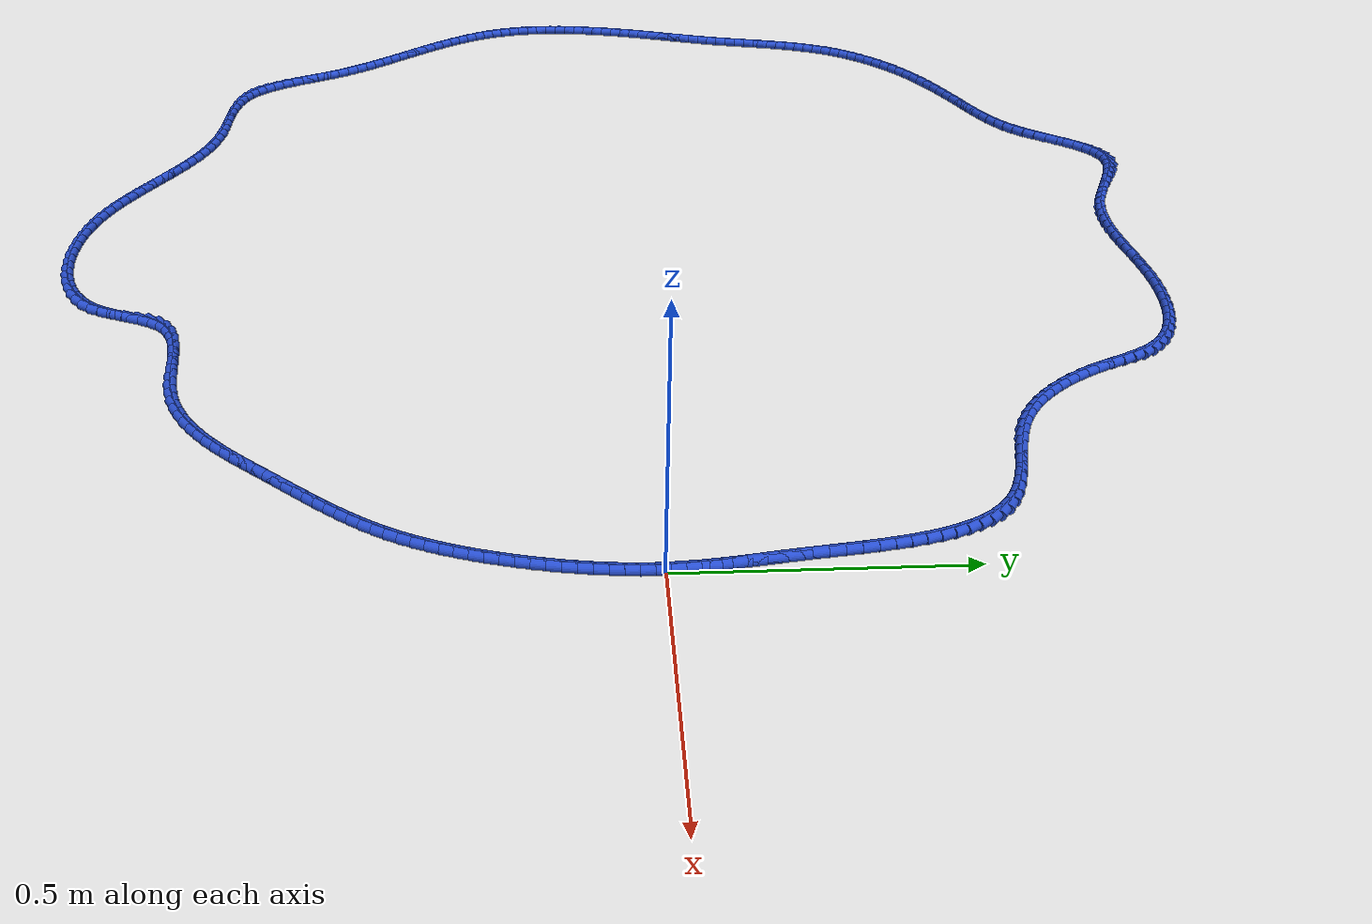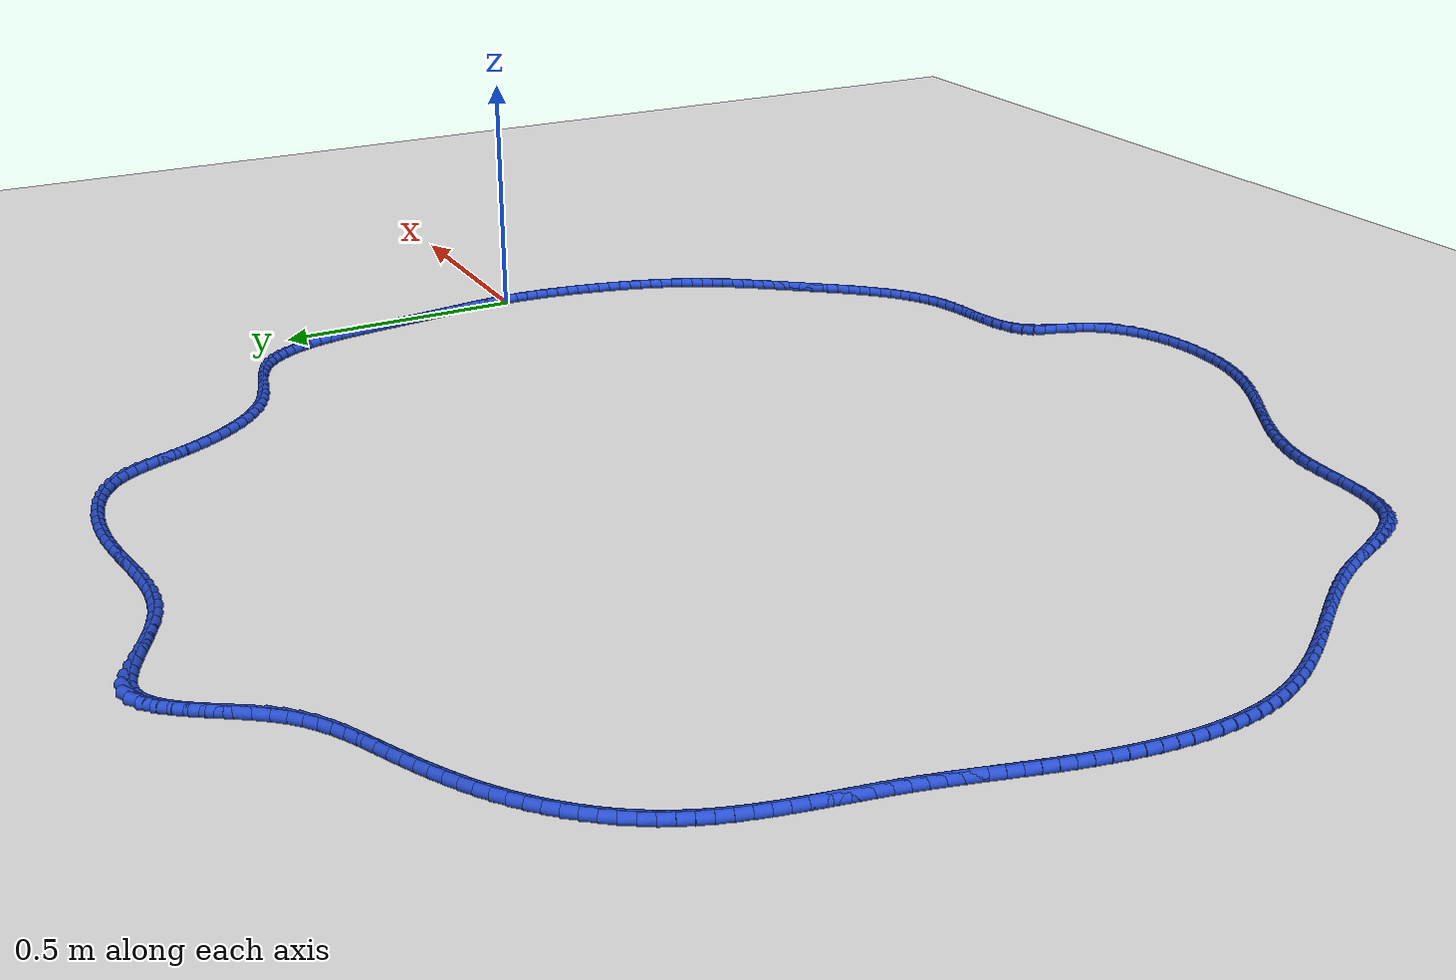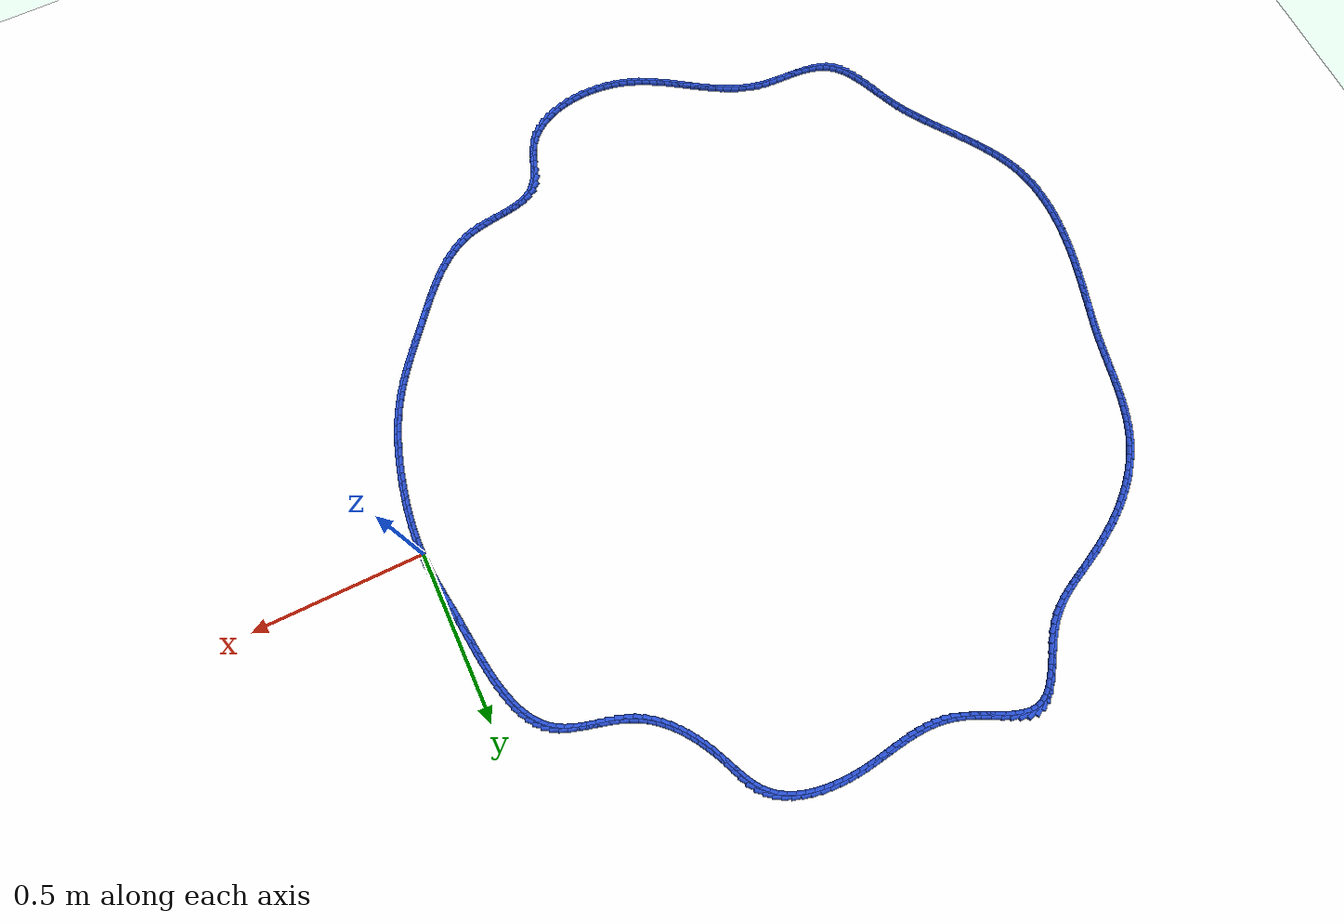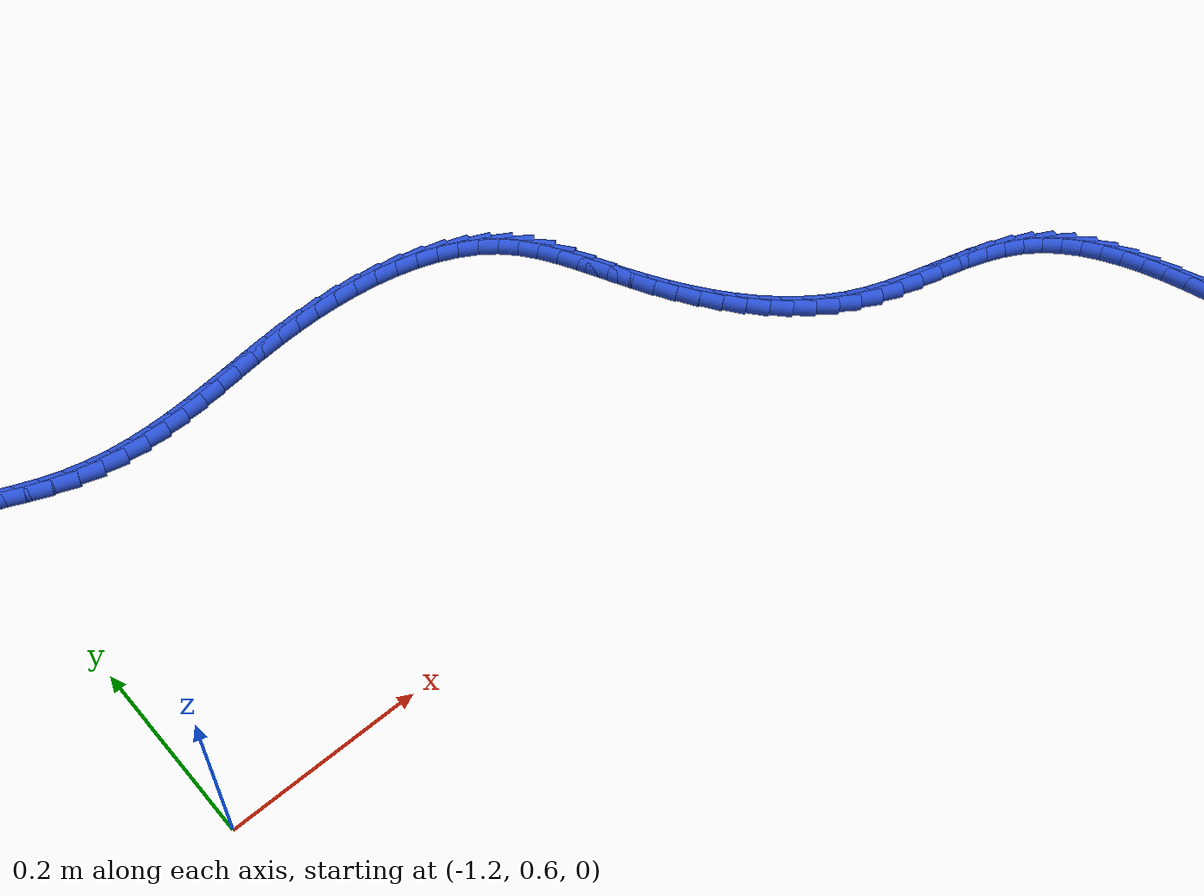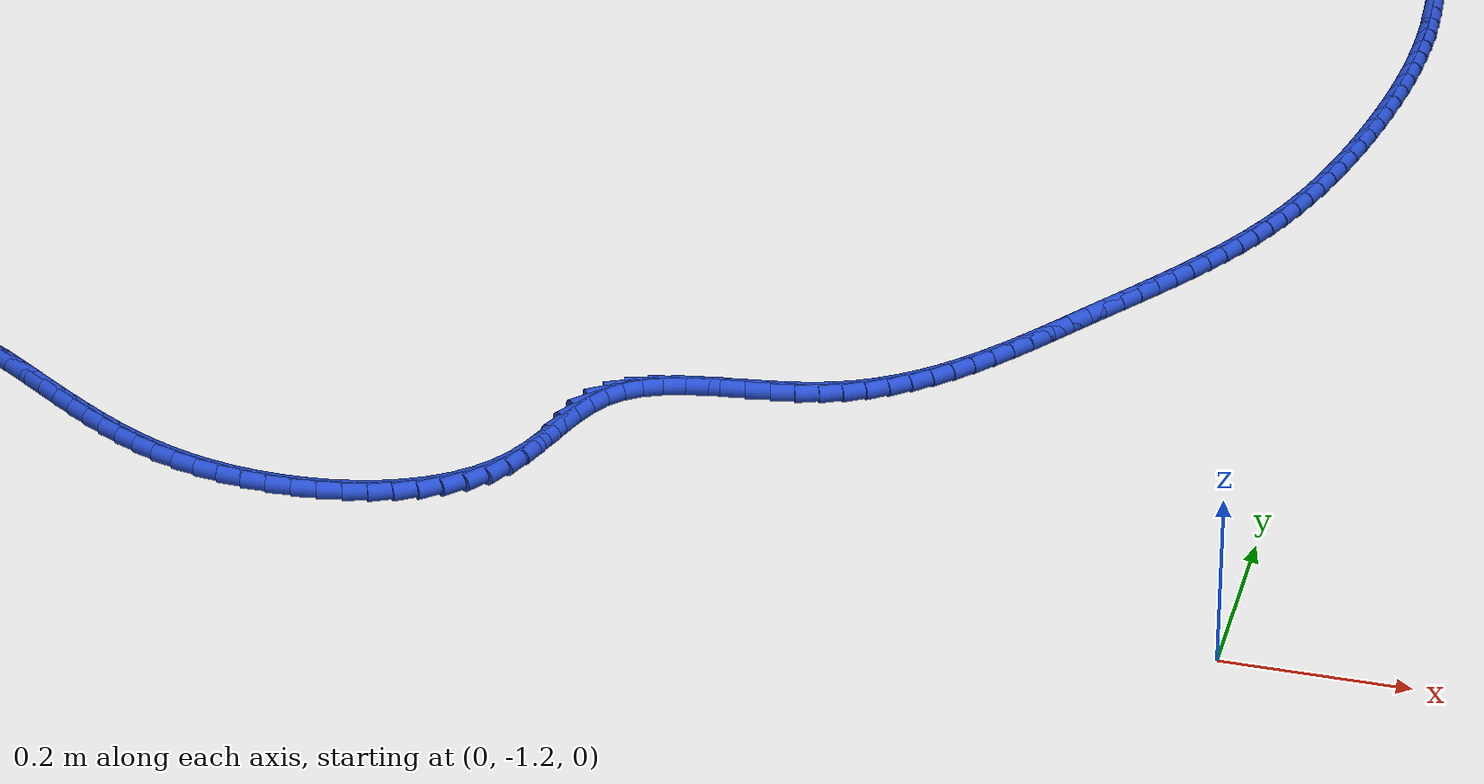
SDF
<sdf version="1.6">
 <world name="default">
  <light name="sun" type="directional">
   <pose>0 0 10 0 -0 0</pose>
   <diffuse>0.8 0.8 0.8 1</diffuse>
   <specular>0.2 0.2 0.2 1</specular>
   <attenuation>
    <range>1000</range>
    <constant>0.9</constant>
    <linear>0.01</linear>
    <quadratic>0.001</quadratic>
   </attenuation>
   <direction>-0.5 0.1 -0.9</direction>
  </light>
  <model name="ground_plane">
   <static>1</static>
   <link name="link">
    <collision name="collision">
     <geometry><plane><normal>0 0 1</normal><size>100 100</size></plane></geometry>
     <surface><friction><ode><mu>100</mu><mu2>50</mu2></ode></friction></surface>
    </collision>
    <visual name="visual">
     <cast_shadows>0</cast_shadows>
     <geometry><plane><normal>0 0 1</normal><size>100 100</size></plane></geometry>
     <material>
      <script><uri>file://media/materials/scripts/gazebo.material</uri><name>Gazebo/WhiteGlow</name></script>
     </material>
    </visual>
   </link>
  </model>
  <gravity>0 0 -9.8</gravity>
  <magnetic_field>6e-06 2.3e-05 -4.2e-05</magnetic_field>
  <atmosphere type="adiabatic"/>
  <physics name="default_physics" default="0" type="ode">
   <max_step_size>0.001</max_step_size>
   <real_time_factor>1</real_time_factor>
   <real_time_update_rate>1000</real_time_update_rate>
  </physics>
  <scene><ambient>0.4 0.4 0.4 1</ambient><background>0.7 0.7 0.7 1</background><shadows>1</shadows></scene>
  <spherical_coordinates>
   <surface_model>EARTH_WGS84</surface_model>
   <latitude_deg>0</latitude_deg>
   <longitude_deg>0</longitude_deg>
   <elevation>0</elevation>
   <heading_deg>0</heading_deg>
  </spherical_coordinates>
  <model name="line">
   <link name="link_0">
    <pose>-1.0408340855860843e-17 4.163336342344337e-17 0.01 0 1.57 -1.5335265531887328</pose>
    <collision name="collision">
     <geometry><cylinder><radius>0.01</radius><length>0.08</length></cylinder></geometry>
    </collision>
    <visual name="visual">
     <material>
      <script><name>Gazebo/Blue</name><uri>file://media/materials/scripts/gazebo.material</uri></script>
     </material>
     <geometry><cylinder><radius>0.01</radius><length>0.08</length></cylinder></geometry>
    </visual>
   </link>
   <link name="link_1">
    <pose>-0.0008815606381045438 0.023642548421452525 0.01 0 1.57 -1.5033334476186593</pose>
    <collision name="collision">
     <geometry><cylinder><radius>0.01</radius><length>0.08</length></cylinder></geometry>
    </collision>
    <visual name="visual">
     <material>
      <script><name>Gazebo/Blue</name><uri>file://media/materials/scripts/gazebo.material</uri></script>
     </material>
     <geometry><cylinder><radius>0.01</radius><length>0.08</length></cylinder></geometry>
    </visual>
   </link>
   <link name="link_2">
    <pose>-0.002472213597452904 0.047184963130246164 0.01 0 1.57 -1.4779685904669417</pose>
    <collision name="collision">
     <geometry><cylinder><radius>0.01</radius><length>0.08</length></cylinder></geometry>
    </collision>
    <visual name="visual">
     <material>
      <script><name>Gazebo/Blue</name><uri>file://media/materials/scripts/gazebo.material</uri></script>
     </material>
     <geometry><cylinder><radius>0.01</radius><length>0.08</length></cylinder></geometry>
    </visual>
   </link>
   <link name="link_3">
    <pose>-0.004663008302395894 0.07071778305130683 0.01 0 1.57 -1.4577037268923556</pose>
    <collision name="collision">
     <geometry><cylinder><radius>0.01</radius><length>0.08</length></cylinder></geometry>
    </collision>
    <visual name="visual">
     <material>
      <script><name>Gazebo/Blue</name><uri>file://media/materials/scripts/gazebo.material</uri></script>
     </material>
     <geometry><cylinder><radius>0.01</radius><length>0.08</length></cylinder></geometry>
    </visual>
   </link>
   <link name="link_4">
    <pose>-0.007344994177284325 0.0943315471095603 0.01 0 1.57 -1.4426731631718936</pose>
    <collision name="collision">
     <geometry><cylinder><radius>0.01</radius><length>0.08</length></cylinder></geometry>
    </collision>
    <visual name="visual">
     <material>
      <script><name>Gazebo/Blue</name><uri>file://media/materials/scripts/gazebo.material</uri></script>
     </material>
     <geometry><cylinder><radius>0.01</radius><length>0.08</length></cylinder></geometry>
    </visual>
   </link>
   <link name="link_5">
    <pose>-0.010409220646469007 0.11811679422993246 0.01 0 1.57 -1.4328874847076394</pose>
    <collision name="collision">
     <geometry><cylinder><radius>0.01</radius><length>0.08</length></cylinder></geometry>
    </collision>
    <visual name="visual">
     <material>
      <script><name>Gazebo/Blue</name><uri>file://media/materials/scripts/gazebo.material</uri></script>
     </material>
     <geometry><cylinder><radius>0.01</radius><length>0.08</length></cylinder></geometry>
    </visual>
   </link>
   <link name="link_6">
    <pose>-0.013746737134300753 0.14216406333734918 0.01 0 1.57 -1.4282500407042749</pose>
    <collision name="collision">
     <geometry><cylinder><radius>0.01</radius><length>0.08</length></cylinder></geometry>
    </collision>
    <visual name="visual">
     <material>
      <script><name>Gazebo/Blue</name><uri>file://media/materials/scripts/gazebo.material</uri></script>
     </material>
     <geometry><cylinder><radius>0.01</radius><length>0.08</length></cylinder></geometry>
    </visual>
   </link>
   <link name="link_7">
    <pose>-0.017248593065130366 0.16656389335673624 0.01 0 1.57 -1.4285736525562691</pose>
    <collision name="collision">
     <geometry><cylinder><radius>0.01</radius><length>0.08</length></cylinder></geometry>
    </collision>
    <visual name="visual">
     <material>
      <script><name>Gazebo/Blue</name><uri>file://media/materials/scripts/gazebo.material</uri></script>
     </material>
     <geometry><cylinder><radius>0.01</radius><length>0.08</length></cylinder></geometry>
    </visual>
   </link>
   <link name="link_8">
    <pose>-0.02080583786330866 0.19140682321301955 0.01 0 1.57 -1.4335960940614685</pose>
    <collision name="collision">
     <geometry><cylinder><radius>0.01</radius><length>0.08</length></cylinder></geometry>
    </collision>
    <visual name="visual">
     <material>
      <script><name>Gazebo/Blue</name><uri>file://media/materials/scripts/gazebo.material</uri></script>
     </material>
     <geometry><cylinder><radius>0.01</radius><length>0.08</length></cylinder></geometry>
    </visual>
   </link>
   <link name="link_9">
    <pose>-0.024309520953186434 0.21678339183112483 0.01 0 1.57 -1.4421229647635574</pose>
    <collision name="collision">
     <geometry><cylinder><radius>0.01</radius><length>0.08</length></cylinder></geometry>
    </collision>
    <visual name="visual">
     <material>
      <script><name>Gazebo/Blue</name><uri>file://media/materials/scripts/gazebo.material</uri></script>
     </material>
     <geometry><cylinder><radius>0.01</radius><length>0.08</length></cylinder></geometry>
    </visual>
   </link>
   <link name="link_10">
    <pose>-0.027670828312121688 0.24276185332578593 0.01 0 1.57 -1.447130718149854</pose>
    <collision name="collision">
     <geometry><cylinder><radius>0.01</radius><length>0.08</length></cylinder></geometry>
    </collision>
    <visual name="visual">
     <material>
      <script><name>Gazebo/Blue</name><uri>file://media/materials/scripts/gazebo.material</uri></script>
     </material>
     <geometry><cylinder><radius>0.01</radius><length>0.08</length></cylinder></geometry>
    </visual>
   </link>
   <link name="link_11">
    <pose>-0.030961202705803523 0.26923310811526735 0.01 0 1.57 -1.4456629101350595</pose>
    <collision name="collision">
     <geometry><cylinder><radius>0.01</radius><length>0.08</length></cylinder></geometry>
    </collision>
    <visual name="visual">
     <material>
      <script><name>Gazebo/Blue</name><uri>file://media/materials/scripts/gazebo.material</uri></script>
     </material>
     <geometry><cylinder><radius>0.01</radius><length>0.08</length></cylinder></geometry>
    </visual>
   </link>
   <link name="link_12">
    <pose>-0.03432864654540235 0.2960033292482925 0.01 0 1.57 -1.4378909385127752</pose>
    <collision name="collision">
     <geometry><cylinder><radius>0.01</radius><length>0.08</length></cylinder></geometry>
    </collision>
    <visual name="visual">
     <material>
      <script><name>Gazebo/Blue</name><uri>file://media/materials/scripts/gazebo.material</uri></script>
     </material>
     <geometry><cylinder><radius>0.01</radius><length>0.08</length></cylinder></geometry>
    </visual>
   </link>
   <link name="link_13">
    <pose>-0.037921637205859636 0.3228781641385625 0.01 0 1.57 -1.4237598934275926</pose>
    <collision name="collision">
     <geometry><cylinder><radius>0.01</radius><length>0.08</length></cylinder></geometry>
    </collision>
    <visual name="visual">
     <material>
      <script><name>Gazebo/Blue</name><uri>file://media/materials/scripts/gazebo.material</uri></script>
     </material>
     <geometry><cylinder><radius>0.01</radius><length>0.08</length></cylinder></geometry>
    </visual>
   </link>
   <link name="link_14">
    <pose>-0.04188865206211683 0.3496632601997785 0.01 0 1.57 -1.4029803419390274</pose>
    <collision name="collision">
     <geometry><cylinder><radius>0.01</radius><length>0.08</length></cylinder></geometry>
    </collision>
    <visual name="visual">
     <material>
      <script><name>Gazebo/Blue</name><uri>file://media/materials/scripts/gazebo.material</uri></script>
     </material>
     <geometry><cylinder><radius>0.01</radius><length>0.08</length></cylinder></geometry>
    </visual>
   </link>
   <link name="link_15">
    <pose>-0.04637816848911541 0.3761642648456414 0.01 0 1.57 -1.3750277220714602</pose>
    <collision name="collision">
     <geometry><cylinder><radius>0.01</radius><length>0.08</length></cylinder></geometry>
    </collision>
    <visual name="visual">
     <material>
      <script><name>Gazebo/Blue</name><uri>file://media/materials/scripts/gazebo.material</uri></script>
     </material>
     <geometry><cylinder><radius>0.01</radius><length>0.08</length></cylinder></geometry>
    </visual>
   </link>
   <link name="link_16">
    <pose>-0.05153866386179685 0.40218682548985274 0.01 0 1.57 -1.3391337930501368</pose>
    <collision name="collision">
     <geometry><cylinder><radius>0.01</radius><length>0.08</length></cylinder></geometry>
    </collision>
    <visual name="visual">
     <material>
      <script><name>Gazebo/Blue</name><uri>file://media/materials/scripts/gazebo.material</uri></script>
     </material>
     <geometry><cylinder><radius>0.01</radius><length>0.08</length></cylinder></geometry>
    </visual>
   </link>
   <link name="link_17">
    <pose>-0.05751861555510259 0.42753658954611323 0.01 0 1.57 -1.2942779838909912</pose>
    <collision name="collision">
     <geometry><cylinder><radius>0.01</radius><length>0.08</length></cylinder></geometry>
    </collision>
    <visual name="visual">
     <material>
      <script><name>Gazebo/Blue</name><uri>file://media/materials/scripts/gazebo.material</uri></script>
     </material>
     <geometry><cylinder><radius>0.01</radius><length>0.08</length></cylinder></geometry>
    </visual>
   </link>
   <link name="link_18">
    <pose>-0.0644665009439741 0.45201920442812416 0.01 0 1.57 -1.239192911731538</pose>
    <collision name="collision">
     <geometry><cylinder><radius>0.01</radius><length>0.08</length></cylinder></geometry>
    </collision>
    <visual name="visual">
     <material>
      <script><name>Gazebo/Blue</name><uri>file://media/materials/scripts/gazebo.material</uri></script>
     </material>
     <geometry><cylinder><radius>0.01</radius><length>0.08</length></cylinder></geometry>
    </visual>
   </link>
   <link name="link_19">
    <pose>-0.07253079740335286 0.47544031754958666 0.01 0 1.57 -1.1724101470219883</pose>
    <collision name="collision">
     <geometry><cylinder><radius>0.01</radius><length>0.08</length></cylinder></geometry>
    </collision>
    <visual name="visual">
     <material>
      <script><name>Gazebo/Blue</name><uri>file://media/materials/scripts/gazebo.material</uri></script>
     </material>
     <geometry><cylinder><radius>0.01</radius><length>0.08</length></cylinder></geometry>
    </visual>
   </link>
   <link name="link_20">
    <pose>-0.08185998230818031 0.49760557632420155 0.01 0 1.57 -1.0923901492039259</pose>
    <collision name="collision">
     <geometry><cylinder><radius>0.01</radius><length>0.08</length></cylinder></geometry>
    </collision>
    <visual name="visual">
     <material>
      <script><name>Gazebo/Blue</name><uri>file://media/materials/scripts/gazebo.material</uri></script>
     </material>
     <geometry><cylinder><radius>0.01</radius><length>0.08</length></cylinder></geometry>
    </visual>
   </link>
   <link name="link_21">
    <pose>-0.09260253303339797 0.5183206281656704 0.01 0 1.57 -0.9977986946641823</pose>
    <collision name="collision">
     <geometry><cylinder><radius>0.01</radius><length>0.08</length></cylinder></geometry>
    </collision>
    <visual name="visual">
     <material>
      <script><name>Gazebo/Blue</name><uri>file://media/materials/scripts/gazebo.material</uri></script>
     </material>
     <geometry><cylinder><radius>0.01</radius><length>0.08</length></cylinder></geometry>
    </visual>
   </link>
   <link name="link_22">
    <pose>-0.10490692695394727 0.5373911204876941 0.01 0 1.57 -0.8879886369406136</pose>
    <collision name="collision">
     <geometry><cylinder><radius>0.01</radius><length>0.08</length></cylinder></geometry>
    </collision>
    <visual name="visual">
     <material>
      <script><name>Gazebo/Blue</name><uri>file://media/materials/scripts/gazebo.material</uri></script>
     </material>
     <geometry><cylinder><radius>0.01</radius><length>0.08</length></cylinder></geometry>
    </visual>
   </link>
   <link name="link_23">
    <pose>-0.11892164144476966 0.5546227007039738 0.01 0 1.57 -0.7636713867671715</pose>
    <collision name="collision">
     <geometry><cylinder><radius>0.01</radius><length>0.08</length></cylinder></geometry>
    </collision>
    <visual name="visual">
     <material>
      <script><name>Gazebo/Blue</name><uri>file://media/materials/scripts/gazebo.material</uri></script>
     </material>
     <geometry><cylinder><radius>0.01</radius><length>0.08</length></cylinder></geometry>
    </visual>
   </link>
   <link name="link_24">
    <pose>-0.1347951538808066 0.5698210162282105 0.01 0 1.57 -0.6275834383459182</pose>
    <collision name="collision">
     <geometry><cylinder><radius>0.01</radius><length>0.08</length></cylinder></geometry>
    </collision>
    <visual name="visual">
     <material>
      <script><name>Gazebo/Blue</name><uri>file://media/materials/scripts/gazebo.material</uri></script>
     </material>
     <geometry><cylinder><radius>0.01</radius><length>0.08</length></cylinder></geometry>
    </visual>
   </link>
   <link name="link_25">
    <pose>-0.15267575117991916 0.5827919592301838 0.01 0 1.57 -0.4939381866768642</pose>
    <collision name="collision">
     <geometry><cylinder><radius>0.01</radius><length>0.08</length></cylinder></geometry>
    </collision>
    <visual name="visual">
     <material>
      <script><name>Gazebo/Blue</name><uri>file://media/materials/scripts/gazebo.material</uri></script>
     </material>
     <geometry><cylinder><radius>0.01</radius><length>0.08</length></cylinder></geometry>
    </visual>
   </link>
   <link name="link_26">
    <pose>-0.1725806281138693 0.5935098881794412 0.01 0 1.57 -0.3911125346922422</pose>
    <collision name="collision">
     <geometry><cylinder><radius>0.01</radius><length>0.08</length></cylinder></geometry>
    </collision>
    <visual name="visual">
     <material>
      <script><name>Gazebo/Blue</name><uri>file://media/materials/scripts/gazebo.material</uri></script>
     </material>
     <geometry><cylinder><radius>0.01</radius><length>0.08</length></cylinder></geometry>
    </visual>
   </link>
   <link name="link_27">
    <pose>-0.1941673604443634 0.6024113073395603 0.01 0 1.57 -0.3208952534931505</pose>
    <collision name="collision">
     <geometry><cylinder><radius>0.01</radius><length>0.08</length></cylinder></geometry>
    </collision>
    <visual name="visual">
     <material>
      <script><name>Gazebo/Blue</name><uri>file://media/materials/scripts/gazebo.material</uri></script>
     </material>
     <geometry><cylinder><radius>0.01</radius><length>0.08</length></cylinder></geometry>
    </visual>
   </link>
   <link name="link_28">
    <pose>-0.21703240450827754 0.61001126544571 0.01 0 1.57 -0.2794964845156658</pose>
    <collision name="collision">
     <geometry><cylinder><radius>0.01</radius><length>0.08</length></cylinder></geometry>
    </collision>
    <visual name="visual">
     <material>
      <script><name>Gazebo/Blue</name><uri>file://media/materials/scripts/gazebo.material</uri></script>
     </material>
     <geometry><cylinder><radius>0.01</radius><length>0.08</length></cylinder></geometry>
    </visual>
   </link>
   <link name="link_29">
    <pose>-0.24077221664248757 0.6168248112330594 0.01 0 1.57 -0.26391209824238027</pose>
    <collision name="collision">
     <geometry><cylinder><radius>0.01</radius><length>0.08</length></cylinder></geometry>
    </collision>
    <visual name="visual">
     <material>
      <script><name>Gazebo/Blue</name><uri>file://media/materials/scripts/gazebo.material</uri></script>
     </material>
     <geometry><cylinder><radius>0.01</radius><length>0.08</length></cylinder></geometry>
    </visual>
   </link>
   <link name="link_30">
    <pose>-0.2649832531838695 0.6233669934367777 0.01 0 1.57 -0.27254368932291256</pose>
    <collision name="collision">
     <geometry><cylinder><radius>0.01</radius><length>0.08</length></cylinder></geometry>
    </collision>
    <visual name="visual">
     <material>
      <script><name>Gazebo/Blue</name><uri>file://media/materials/scripts/gazebo.material</uri></script>
     </material>
     <geometry><cylinder><radius>0.01</radius><length>0.08</length></cylinder></geometry>
    </visual>
   </link>
   <link name="link_31">
    <pose>-0.28926197046929925 0.630152860792034 0.01 0 1.57 -0.30525969146622467</pose>
    <collision name="collision">
     <geometry><cylinder><radius>0.01</radius><length>0.08</length></cylinder></geometry>
    </collision>
    <visual name="visual">
     <material>
      <script><name>Gazebo/Blue</name><uri>file://media/materials/scripts/gazebo.material</uri></script>
     </material>
     <geometry><cylinder><radius>0.01</radius><length>0.08</length></cylinder></geometry>
    </visual>
   </link>
   <link name="link_32">
    <pose>-0.3132048248356526 0.6376974620339968 0.01 0 1.57 -0.3631874440926667</pose>
    <collision name="collision">
     <geometry><cylinder><radius>0.01</radius><length>0.08</length></cylinder></geometry>
    </collision>
    <visual name="visual">
     <material>
      <script><name>Gazebo/Blue</name><uri>file://media/materials/scripts/gazebo.material</uri></script>
     </material>
     <geometry><cylinder><radius>0.01</radius><length>0.08</length></cylinder></geometry>
    </visual>
   </link>
   <link name="link_33">
    <pose>-0.3364082726198057 0.6465158458978358 0.01 0 1.57 -0.4474529683519637</pose>
    <collision name="collision">
     <geometry><cylinder><radius>0.01</radius><length>0.08</length></cylinder></geometry>
    </collision>
    <visual name="visual">
     <material>
      <script><name>Gazebo/Blue</name><uri>file://media/materials/scripts/gazebo.material</uri></script>
     </material>
     <geometry><cylinder><radius>0.01</radius><length>0.08</length></cylinder></geometry>
    </visual>
   </link>
   <link name="link_34">
    <pose>-0.35847890117476733 0.6571079280459454 0.01 0 1.57 -0.5431304937333896</pose>
    <collision name="collision">
     <geometry><cylinder><radius>0.01</radius><length>0.08</length></cylinder></geometry>
    </collision>
    <visual name="visual">
     <material>
      <script><name>Gazebo/Blue</name><uri>file://media/materials/scripts/gazebo.material</uri></script>
     </material>
     <geometry><cylinder><radius>0.01</radius><length>0.08</length></cylinder></geometry>
    </visual>
   </link>
   <link name="link_35">
    <pose>-0.37924413398741486 0.6696437530555999 0.01 0 1.57 -0.6336956714926293</pose>
    <collision name="collision">
     <geometry><cylinder><radius>0.01</radius><length>0.08</length></cylinder></geometry>
    </collision>
    <visual name="visual">
     <material>
      <script><name>Gazebo/Blue</name><uri>file://media/materials/scripts/gazebo.material</uri></script>
     </material>
     <geometry><cylinder><radius>0.01</radius><length>0.08</length></cylinder></geometry>
    </visual>
   </link>
   <link name="link_36">
    <pose>-0.3987456701961418 0.6839732940536191 0.01 0 1.57 -0.7175199030941809</pose>
    <collision name="collision">
     <geometry><cylinder><radius>0.01</radius><length>0.08</length></cylinder></geometry>
    </collision>
    <visual name="visual">
     <material>
      <script><name>Gazebo/Blue</name><uri>file://media/materials/scripts/gazebo.material</uri></script>
     </material>
     <geometry><cylinder><radius>0.01</radius><length>0.08</length></cylinder></geometry>
    </visual>
   </link>
   <link name="link_37">
    <pose>-0.41703402748490576 0.699933351579786 0.01 0 1.57 -0.7941288165803341</pose>
    <collision name="collision">
     <geometry><cylinder><radius>0.01</radius><length>0.08</length></cylinder></geometry>
    </collision>
    <visual name="visual">
     <material>
      <script><name>Gazebo/Blue</name><uri>file://media/materials/scripts/gazebo.material</uri></script>
     </material>
     <geometry><cylinder><radius>0.01</radius><length>0.08</length></cylinder></geometry>
    </visual>
   </link>
   <link name="link_38">
    <pose>-0.4341597235376636 0.7173607261738832 0.01 0 1.57 -0.8634644352262602</pose>
    <collision name="collision">
     <geometry><cylinder><radius>0.01</radius><length>0.08</length></cylinder></geometry>
    </collision>
    <visual name="visual">
     <material>
      <script><name>Gazebo/Blue</name><uri>file://media/materials/scripts/gazebo.material</uri></script>
     </material>
     <geometry><cylinder><radius>0.01</radius><length>0.08</length></cylinder></geometry>
    </visual>
   </link>
   <link name="link_39">
    <pose>-0.4501732760383726 0.7360922183756939 0.01 0 1.57 -0.9257633937367337</pose>
    <collision name="collision">
     <geometry><cylinder><radius>0.01</radius><length>0.08</length></cylinder></geometry>
    </collision>
    <visual name="visual">
     <material>
      <script><name>Gazebo/Blue</name><uri>file://media/materials/scripts/gazebo.material</uri></script>
     </material>
     <geometry><cylinder><radius>0.01</radius><length>0.08</length></cylinder></geometry>
    </visual>
   </link>
   <link name="link_40">
    <pose>-0.46512520267099 0.7559646287250008 0.01 0 1.57 -0.9814424630135068</pose>
    <collision name="collision">
     <geometry><cylinder><radius>0.01</radius><length>0.08</length></cylinder></geometry>
    </collision>
    <visual name="visual">
     <material>
      <script><name>Gazebo/Blue</name><uri>file://media/materials/scripts/gazebo.material</uri></script>
     </material>
     <geometry><cylinder><radius>0.01</radius><length>0.08</length></cylinder></geometry>
    </visual>
   </link>
   <link name="link_41">
    <pose>-0.479066021119473 0.7768147577615864 0.01 0 1.57 -1.0310070218489655</pose>
    <collision name="collision">
     <geometry><cylinder><radius>0.01</radius><length>0.08</length></cylinder></geometry>
    </collision>
    <visual name="visual">
     <material>
      <script><name>Gazebo/Blue</name><uri>file://media/materials/scripts/gazebo.material</uri></script>
     </material>
     <geometry><cylinder><radius>0.01</radius><length>0.08</length></cylinder></geometry>
    </visual>
   </link>
   <link name="link_42">
    <pose>-0.4920462490677786 0.7984794060252336 0.01 0 1.57 -1.074985651485482</pose>
    <collision name="collision">
     <geometry><cylinder><radius>0.01</radius><length>0.08</length></cylinder></geometry>
    </collision>
    <visual name="visual">
     <material>
      <script><name>Gazebo/Blue</name><uri>file://media/materials/scripts/gazebo.material</uri></script>
     </material>
     <geometry><cylinder><radius>0.01</radius><length>0.08</length></cylinder></geometry>
    </visual>
   </link>
   <link name="link_43">
    <pose>-0.5041164041998645 0.8207953740557256 0.01 0 1.57 -1.1138864565512858</pose>
    <collision name="collision">
     <geometry><cylinder><radius>0.01</radius><length>0.08</length></cylinder></geometry>
    </collision>
    <visual name="visual">
     <material>
      <script><name>Gazebo/Blue</name><uri>file://media/materials/scripts/gazebo.material</uri></script>
     </material>
     <geometry><cylinder><radius>0.01</radius><length>0.08</length></cylinder></geometry>
    </visual>
   </link>
   <link name="link_44">
    <pose>-0.515327024153798 0.8435994497952456 0.01 0 1.57 -1.1430391814062826</pose>
    <collision name="collision">
     <geometry><cylinder><radius>0.01</radius><length>0.08</length></cylinder></geometry>
    </collision>
    <visual name="visual">
     <material>
      <script><name>Gazebo/Blue</name><uri>file://media/materials/scripts/gazebo.material</uri></script>
     </material>
     <geometry><cylinder><radius>0.01</radius><length>0.08</length></cylinder></geometry>
    </visual>
   </link>
   <link name="link_45">
    <pose>-0.5258397549877789 0.8666582752708383 0.01 0 1.57 -1.1454804708642452</pose>
    <collision name="collision">
     <geometry><cylinder><radius>0.01</radius><length>0.08</length></cylinder></geometry>
    </collision>
    <visual name="visual">
     <material>
      <script><name>Gazebo/Blue</name><uri>file://media/materials/scripts/gazebo.material</uri></script>
     </material>
     <geometry><cylinder><radius>0.01</radius><length>0.08</length></cylinder></geometry>
    </visual>
   </link>
   <link name="link_46">
    <pose>-0.5361879579658857 0.8895038180964252 0.01 0 1.57 -1.1167049565069889</pose>
    <collision name="collision">
     <geometry><cylinder><radius>0.01</radius><length>0.08</length></cylinder></geometry>
    </collision>
    <visual name="visual">
     <material>
      <script><name>Gazebo/Blue</name><uri>file://media/materials/scripts/gazebo.material</uri></script>
     </material>
     <geometry><cylinder><radius>0.01</radius><length>0.08</length></cylinder></geometry>
    </visual>
   </link>
   <link name="link_47">
    <pose>-0.5469826380340865 0.9116190272146653 0.01 0 1.57 -1.0542662585774825</pose>
    <collision name="collision">
     <geometry><cylinder><radius>0.01</radius><length>0.08</length></cylinder></geometry>
    </collision>
    <visual name="visual">
     <material>
      <script><name>Gazebo/Blue</name><uri>file://media/materials/scripts/gazebo.material</uri></script>
     </material>
     <geometry><cylinder><radius>0.01</radius><length>0.08</length></cylinder></geometry>
    </visual>
   </link>
   <link name="link_48">
    <pose>-0.5588348001383497 0.9324868515682173 0.01 0 1.57 -0.9548800586331992</pose>
    <collision name="collision">
     <geometry><cylinder><radius>0.01</radius><length>0.08</length></cylinder></geometry>
    </collision>
    <visual name="visual">
     <material>
      <script><name>Gazebo/Blue</name><uri>file://media/materials/scripts/gazebo.material</uri></script>
     </material>
     <geometry><cylinder><radius>0.01</radius><length>0.08</length></cylinder></geometry>
    </visual>
   </link>
   <link name="link_49">
    <pose>-0.5723554492246438 0.9515902400997405 0.01 0 1.57 -0.8179550583791481</pose>
    <collision name="collision">
     <geometry><cylinder><radius>0.01</radius><length>0.08</length></cylinder></geometry>
    </collision>
    <visual name="visual">
     <material>
      <script><name>Gazebo/Blue</name><uri>file://media/materials/scripts/gazebo.material</uri></script>
     </material>
     <geometry><cylinder><radius>0.01</radius><length>0.08</length></cylinder></geometry>
    </visual>
   </link>
   <link name="link_50">
    <pose>-0.5881319767385045 0.9684289952767251 0.01 0 1.57 -0.6705664116566687</pose>
    <collision name="collision">
     <geometry><cylinder><radius>0.01</radius><length>0.08</length></cylinder></geometry>
    </collision>
    <visual name="visual">
     <material>
      <script><name>Gazebo/Blue</name><uri>file://media/materials/scripts/gazebo.material</uri></script>
     </material>
     <geometry><cylinder><radius>0.01</radius><length>0.08</length></cylinder></geometry>
    </visual>
   </link>
   <link name="link_51">
    <pose>-0.6062906542935942 0.9828320319131779 0.01 0 1.57 -0.5385052175458477</pose>
    <collision name="collision">
     <geometry><cylinder><radius>0.01</radius><length>0.08</length></cylinder></geometry>
    </collision>
    <visual name="visual">
     <material>
      <script><name>Gazebo/Blue</name><uri>file://media/materials/scripts/gazebo.material</uri></script>
     </material>
     <geometry><cylinder><radius>0.01</radius><length>0.08</length></cylinder></geometry>
    </visual>
   </link>
   <link name="link_52">
    <pose>-0.6265380501189136 0.994927817252256 0.01 0 1.57 -0.42344300470566193</pose>
    <collision name="collision">
     <geometry><cylinder><radius>0.01</radius><length>0.08</length></cylinder></geometry>
    </collision>
    <visual name="visual">
     <material>
      <script><name>Gazebo/Blue</name><uri>file://media/materials/scripts/gazebo.material</uri></script>
     </material>
     <geometry><cylinder><radius>0.01</radius><length>0.08</length></cylinder></geometry>
    </visual>
   </link>
   <link name="link_53">
    <pose>-0.6485654252368007 1.004855743659729 0.01 0 1.57 -0.3242987128208899</pose>
    <collision name="collision">
     <geometry><cylinder><radius>0.01</radius><length>0.08</length></cylinder></geometry>
    </collision>
    <visual name="visual">
     <material>
      <script><name>Gazebo/Blue</name><uri>file://media/materials/scripts/gazebo.material</uri></script>
     </material>
     <geometry><cylinder><radius>0.01</radius><length>0.08</length></cylinder></geometry>
    </visual>
   </link>
   <link name="link_54">
    <pose>-0.6720640406695941 1.0127552035013687 0.01 0 1.57 -0.23905856530614733</pose>
    <collision name="collision">
     <geometry><cylinder><radius>0.01</radius><length>0.08</length></cylinder></geometry>
    </collision>
    <visual name="visual">
     <material>
      <script><name>Gazebo/Blue</name><uri>file://media/materials/scripts/gazebo.material</uri></script>
     </material>
     <geometry><cylinder><radius>0.01</radius><length>0.08</length></cylinder></geometry>
    </visual>
   </link>
   <link name="link_55">
    <pose>-0.6967251574396328 1.018765589142946 0.01 0 1.57 -0.1654622695289538</pose>
    <collision name="collision">
     <geometry><cylinder><radius>0.01</radius><length>0.08</length></cylinder></geometry>
    </collision>
    <visual name="visual">
     <material>
      <script><name>Gazebo/Blue</name><uri>file://media/materials/scripts/gazebo.material</uri></script>
     </material>
     <geometry><cylinder><radius>0.01</radius><length>0.08</length></cylinder></geometry>
    </visual>
   </link>
   <link name="link_56">
    <pose>-0.7222400365692545 1.0230262929502314 0.01 0 1.57 -0.1013561791781203</pose>
    <collision name="collision">
     <geometry><cylinder><radius>0.01</radius><length>0.08</length></cylinder></geometry>
    </collision>
    <visual name="visual">
     <material>
      <script><name>Gazebo/Blue</name><uri>file://media/materials/scripts/gazebo.material</uri></script>
     </material>
     <geometry><cylinder><radius>0.01</radius><length>0.08</length></cylinder></geometry>
    </visual>
   </link>
   <link name="link_57">
    <pose>-0.7482999390807981 1.0256767072889958 0.01 0 1.57 -0.044825021189955454</pose>
    <collision name="collision">
     <geometry><cylinder><radius>0.01</radius><length>0.08</length></cylinder></geometry>
    </collision>
    <visual name="visual">
     <material>
      <script><name>Gazebo/Blue</name><uri>file://media/materials/scripts/gazebo.material</uri></script>
     </material>
     <geometry><cylinder><radius>0.01</radius><length>0.08</length></cylinder></geometry>
    </visual>
   </link>
   <link name="link_58">
    <pose>-0.7745961259966018 1.0268562245250101 0.01 0 1.57 0.005795734840312658</pose>
    <collision name="collision">
     <geometry><cylinder><radius>0.01</radius><length>0.08</length></cylinder></geometry>
    </collision>
    <visual name="visual">
     <material>
      <script><name>Gazebo/Blue</name><uri>file://media/materials/scripts/gazebo.material</uri></script>
     </material>
     <geometry><cylinder><radius>0.01</radius><length>0.08</length></cylinder></geometry>
    </visual>
   </link>
   <link name="link_59">
    <pose>-0.800819858339004 1.0267042370240456 0.01 0 1.57 0.05180352897620178</pose>
    <collision name="collision">
     <geometry><cylinder><radius>0.01</radius><length>0.08</length></cylinder></geometry>
    </collision>
    <visual name="visual">
     <material>
      <script><name>Gazebo/Blue</name><uri>file://media/materials/scripts/gazebo.material</uri></script>
     </material>
     <geometry><cylinder><radius>0.01</radius><length>0.08</length></cylinder></geometry>
    </visual>
   </link>
   <link name="link_60">
    <pose>-0.8266719919961103 1.0253638059917194 0.01 0 1.57 0.09097652016335105</pose>
    <collision name="collision">
     <geometry><cylinder><radius>0.01</radius><length>0.08</length></cylinder></geometry>
    </collision>
    <visual name="visual">
     <material>
      <script><name>Gazebo/Blue</name><uri>file://media/materials/scripts/gazebo.material</uri></script>
     </material>
     <geometry><cylinder><radius>0.01</radius><length>0.08</length></cylinder></geometry>
    </visual>
   </link>
   <link name="link_61">
    <pose>-0.8520403675194744 1.023049490953751 0.01 0 1.57 0.12004342587354605</pose>
    <collision name="collision">
     <geometry><cylinder><radius>0.01</radius><length>0.08</length></cylinder></geometry>
    </collision>
    <visual name="visual">
     <material>
      <script><name>Gazebo/Blue</name><uri>file://media/materials/scripts/gazebo.material</uri></script>
     </material>
     <geometry><cylinder><radius>0.01</radius><length>0.08</length></cylinder></geometry>
    </visual>
   </link>
   <link name="link_62">
    <pose>-0.8769828090884937 1.020040848979572 0.01 0 1.57 0.1382888419318313</pose>
    <collision name="collision">
     <geometry><cylinder><radius>0.01</radius><length>0.08</length></cylinder></geometry>
    </collision>
    <visual name="visual">
     <material>
      <script><name>Gazebo/Blue</name><uri>file://media/materials/scripts/gazebo.material</uri></script>
     </material>
     <geometry><cylinder><radius>0.01</radius><length>0.08</length></cylinder></geometry>
    </visual>
   </link>
   <link name="link_63">
    <pose>-0.9015633258527398 1.016619802118548 0.01 0 1.57 0.14522849882930947</pose>
    <collision name="collision">
     <geometry><cylinder><radius>0.01</radius><length>0.08</length></cylinder></geometry>
    </collision>
    <visual name="visual">
     <material>
      <script><name>Gazebo/Blue</name><uri>file://media/materials/scripts/gazebo.material</uri></script>
     </material>
     <geometry><cylinder><radius>0.01</radius><length>0.08</length></cylinder></geometry>
    </visual>
   </link>
   <link name="link_64">
    <pose>-0.9258459269617842 1.013068272420046 0.01 0 1.57 0.14045266396409087</pose>
    <collision name="collision">
     <geometry><cylinder><radius>0.01</radius><length>0.08</length></cylinder></geometry>
    </collision>
    <visual name="visual">
     <material>
      <script><name>Gazebo/Blue</name><uri>file://media/materials/scripts/gazebo.material</uri></script>
     </material>
     <geometry><cylinder><radius>0.01</radius><length>0.08</length></cylinder></geometry>
    </visual>
   </link>
   <link name="link_65">
    <pose>-0.9498946215651989 1.0096681819334323 0.01 0 1.57 0.12360774929353104</pose>
    <collision name="collision">
     <geometry><cylinder><radius>0.01</radius><length>0.08</length></cylinder></geometry>
    </collision>
    <visual name="visual">
     <material>
      <script><name>Gazebo/Blue</name><uri>file://media/materials/scripts/gazebo.material</uri></script>
     </material>
     <geometry><cylinder><radius>0.01</radius><length>0.08</length></cylinder></geometry>
    </visual>
   </link>
   <link name="link_66">
    <pose>-0.9737734188125546 1.0067014527080729 0.01 0 1.57 0.09442473405715081</pose>
    <collision name="collision">
     <geometry><cylinder><radius>0.01</radius><length>0.08</length></cylinder></geometry>
    </collision>
    <visual name="visual">
     <material>
      <script><name>Gazebo/Blue</name><uri>file://media/materials/scripts/gazebo.material</uri></script>
     </material>
     <geometry><cylinder><radius>0.01</radius><length>0.08</length></cylinder></geometry>
    </visual>
   </link>
   <link name="link_67">
    <pose>-0.9975463278534236 1.0044500067933348 0.01 0 1.57 0.05280321403246875</pose>
    <collision name="collision">
     <geometry><cylinder><radius>0.01</radius><length>0.08</length></cylinder></geometry>
    </collision>
    <visual name="visual">
     <material>
      <script><name>Gazebo/Blue</name><uri>file://media/materials/scripts/gazebo.material</uri></script>
     </material>
     <geometry><cylinder><radius>0.01</radius><length>0.08</length></cylinder></geometry>
    </visual>
   </link>
   <link name="link_68">
    <pose>-1.021277357837377 1.003195766238584 0.01 0 1.57 -0.001047727772502265</pose>
    <collision name="collision">
     <geometry><cylinder><radius>0.01</radius><length>0.08</length></cylinder></geometry>
    </collision>
    <visual name="visual">
     <material>
      <script><name>Gazebo/Blue</name><uri>file://media/materials/scripts/gazebo.material</uri></script>
     </material>
     <geometry><cylinder><radius>0.01</radius><length>0.08</length></cylinder></geometry>
    </visual>
   </link>
   <link name="link_69">
    <pose>-1.0450305179139865 1.0032206530931873 0.01 0 1.57 -0.06642824713619397</pose>
    <collision name="collision">
     <geometry><cylinder><radius>0.01</radius><length>0.08</length></cylinder></geometry>
    </collision>
    <visual name="visual">
     <material>
      <script><name>Gazebo/Blue</name><uri>file://media/materials/scripts/gazebo.material</uri></script>
     </material>
     <geometry><cylinder><radius>0.01</radius><length>0.08</length></cylinder></geometry>
    </visual>
   </link>
   <link name="link_70">
    <pose>-1.0688698172328237 1.0048065894065108 0.01 0 1.57 -0.14197237797413534</pose>
    <collision name="collision">
     <geometry><cylinder><radius>0.01</radius><length>0.08</length></cylinder></geometry>
    </collision>
    <visual name="visual">
     <material>
      <script><name>Gazebo/Blue</name><uri>file://media/materials/scripts/gazebo.material</uri></script>
     </material>
     <geometry><cylinder><radius>0.01</radius><length>0.08</length></cylinder></geometry>
    </visual>
   </link>
   <link name="link_71">
    <pose>-1.0928592649434599 1.0082354972279208 0.01 0 1.57 -0.22555711141883675</pose>
    <collision name="collision">
     <geometry><cylinder><radius>0.01</radius><length>0.08</length></cylinder></geometry>
    </collision>
    <visual name="visual">
     <material>
      <script><name>Gazebo/Blue</name><uri>file://media/materials/scripts/gazebo.material</uri></script>
     </material>
     <geometry><cylinder><radius>0.01</radius><length>0.08</length></cylinder></geometry>
    </visual>
   </link>
   <link name="link_72">
    <pose>-1.1170628701954666 1.0137892986067842 0.01 0 1.57 -0.3134832671092745</pose>
    <collision name="collision">
     <geometry><cylinder><radius>0.01</radius><length>0.08</length></cylinder></geometry>
    </collision>
    <visual name="visual">
     <material>
      <script><name>Gazebo/Blue</name><uri>file://media/materials/scripts/gazebo.material</uri></script>
     </material>
     <geometry><cylinder><radius>0.01</radius><length>0.08</length></cylinder></geometry>
    </visual>
   </link>
   <link name="link_73">
    <pose>-1.1415386250931434 1.021723665137857 0.01 0 1.57 -0.38495843023401094</pose>
    <collision name="collision">
     <geometry><cylinder><radius>0.01</radius><length>0.08</length></cylinder></geometry>
    </collision>
    <visual name="visual">
     <material>
      <script><name>Gazebo/Blue</name><uri>file://media/materials/scripts/gazebo.material</uri></script>
     </material>
     <geometry><cylinder><radius>0.01</radius><length>0.08</length></cylinder></geometry>
    </visual>
   </link>
   <link name="link_74">
    <pose>-1.1662131491517784 1.0317211315972954 0.01 0 1.57 -0.4256793121092552</pose>
    <collision name="collision">
     <geometry><cylinder><radius>0.01</radius><length>0.08</length></cylinder></geometry>
    </collision>
    <visual name="visual">
     <material>
      <script><name>Gazebo/Blue</name><uri>file://media/materials/scripts/gazebo.material</uri></script>
     </material>
     <geometry><cylinder><radius>0.01</radius><length>0.08</length></cylinder></geometry>
    </visual>
   </link>
   <link name="link_75">
    <pose>-1.1908854745630004 1.042907609851355 0.01 0 1.57 -0.43870521807391655</pose>
    <collision name="collision">
     <geometry><cylinder><radius>0.01</radius><length>0.08</length></cylinder></geometry>
    </collision>
    <visual name="visual">
     <material>
      <script><name>Gazebo/Blue</name><uri>file://media/materials/scripts/gazebo.material</uri></script>
     </material>
     <geometry><cylinder><radius>0.01</radius><length>0.08</length></cylinder></geometry>
    </visual>
   </link>
   <link name="link_76">
    <pose>-1.2153493737290977 1.054386064978441 0.01 0 1.57 -0.4246242303429826</pose>
    <collision name="collision">
     <geometry><cylinder><radius>0.01</radius><length>0.08</length></cylinder></geometry>
    </collision>
    <visual name="visual">
     <material>
      <script><name>Gazebo/Blue</name><uri>file://media/materials/scripts/gazebo.material</uri></script>
     </material>
     <geometry><cylinder><radius>0.01</radius><length>0.08</length></cylinder></geometry>
    </visual>
   </link>
   <link name="link_77">
    <pose>-1.2393986190523578 1.0652594620569584 0.01 0 1.57 -0.380504852113136</pose>
    <collision name="collision">
     <geometry><cylinder><radius>0.01</radius><length>0.08</length></cylinder></geometry>
    </collision>
    <visual name="visual">
     <material>
      <script><name>Gazebo/Blue</name><uri>file://media/materials/scripts/gazebo.material</uri></script>
     </material>
     <geometry><cylinder><radius>0.01</radius><length>0.08</length></cylinder></geometry>
    </visual>
   </link>
   <link name="link_78">
    <pose>-1.262826982935069 1.0746307661653134 0.01 0 1.57 -0.2992240411870275</pose>
    <collision name="collision">
     <geometry><cylinder><radius>0.01</radius><length>0.08</length></cylinder></geometry>
    </collision>
    <visual name="visual">
     <material>
      <script><name>Gazebo/Blue</name><uri>file://media/materials/scripts/gazebo.material</uri></script>
     </material>
     <geometry><cylinder><radius>0.01</radius><length>0.08</length></cylinder></geometry>
    </visual>
   </link>
   <link name="link_79">
    <pose>-1.2854282377795185 1.0816029423819105 0.01 0 1.57 -0.1688167500045451</pose>
    <collision name="collision">
     <geometry><cylinder><radius>0.01</radius><length>0.08</length></cylinder></geometry>
    </collision>
    <visual name="visual">
     <material>
      <script><name>Gazebo/Blue</name><uri>file://media/materials/scripts/gazebo.material</uri></script>
     </material>
     <geometry><cylinder><radius>0.01</radius><length>0.08</length></cylinder></geometry>
    </visual>
   </link>
   <link name="link_80">
    <pose>-1.3069961559879946 1.0852789557851543 0.01 0 1.57 0.025436038229379905</pose>
    <collision name="collision">
     <geometry><cylinder><radius>0.01</radius><length>0.08</length></cylinder></geometry>
    </collision>
    <visual name="visual">
     <material>
      <script><name>Gazebo/Blue</name><uri>file://media/materials/scripts/gazebo.material</uri></script>
     </material>
     <geometry><cylinder><radius>0.01</radius><length>0.08</length></cylinder></geometry>
    </visual>
   </link>
   <link name="link_81">
    <pose>-1.3273245099627844 1.0847617714534512 0.01 0 1.57 0.2852766823593443</pose>
    <collision name="collision">
     <geometry><cylinder><radius>0.01</radius><length>0.08</length></cylinder></geometry>
    </collision>
    <visual name="visual">
     <material>
      <script><name>Gazebo/Blue</name><uri>file://media/materials/scripts/gazebo.material</uri></script>
     </material>
     <geometry><cylinder><radius>0.01</radius><length>0.08</length></cylinder></geometry>
    </visual>
   </link>
   <link name="link_82">
    <pose>-1.346225448578817 1.0792185786723034 0.01 0 1.57 0.5372466858652357</pose>
    <collision name="collision">
     <geometry><cylinder><radius>0.01</radius><length>0.08</length></cylinder></geometry>
    </collision>
    <visual name="visual">
     <material>
      <script><name>Gazebo/Blue</name><uri>file://media/materials/scripts/gazebo.material</uri></script>
     </material>
     <geometry><cylinder><radius>0.01</radius><length>0.08</length></cylinder></geometry>
    </visual>
   </link>
   <link name="link_83">
    <pose>-1.3637812652330452 1.0687606988285516 0.01 0 1.57 0.7224839115204642</pose>
    <collision name="collision">
     <geometry><cylinder><radius>0.01</radius><length>0.08</length></cylinder></geometry>
    </collision>
    <visual name="visual">
     <material>
      <script><name>Gazebo/Blue</name><uri>file://media/materials/scripts/gazebo.material</uri></script>
     </material>
     <geometry><cylinder><radius>0.01</radius><length>0.08</length></cylinder></geometry>
    </visual>
   </link>
   <link name="link_84">
    <pose>-1.380279772194519 1.0542177242668274 0.01 0 1.57 0.8463802153047483</pose>
    <collision name="collision">
     <geometry><cylinder><radius>0.01</radius><length>0.08</length></cylinder></geometry>
    </collision>
    <visual name="visual">
     <material>
      <script><name>Gazebo/Blue</name><uri>file://media/materials/scripts/gazebo.material</uri></script>
     </material>
     <geometry><cylinder><radius>0.01</radius><length>0.08</length></cylinder></geometry>
    </visual>
   </link>
   <link name="link_85">
    <pose>-1.3960139294172942 1.0364372380525244 0.01 0 1.57 0.9230268362988991</pose>
    <collision name="collision">
     <geometry><cylinder><radius>0.01</radius><length>0.08</length></cylinder></geometry>
    </collision>
    <visual name="visual">
     <material>
      <script><name>Gazebo/Blue</name><uri>file://media/materials/scripts/gazebo.material</uri></script>
     </material>
     <geometry><cylinder><radius>0.01</radius><length>0.08</length></cylinder></geometry>
    </visual>
   </link>
   <link name="link_86">
    <pose>-1.4112766968554273 1.0162668232510383 0.01 0 1.57 0.9636212690488895</pose>
    <collision name="collision">
     <geometry><cylinder><radius>0.01</radius><length>0.08</length></cylinder></geometry>
    </collision>
    <visual name="visual">
     <material>
      <script><name>Gazebo/Blue</name><uri>file://media/materials/scripts/gazebo.material</uri></script>
     </material>
     <geometry><cylinder><radius>0.01</radius><length>0.08</length></cylinder></geometry>
    </visual>
   </link>
   <link name="link_87">
    <pose>-1.4263610344629738 0.9945540629277625 0.01 0 1.57 0.9747877971718452</pose>
    <collision name="collision">
     <geometry><cylinder><radius>0.01</radius><length>0.08</length></cylinder></geometry>
    </collision>
    <visual name="visual">
     <material>
      <script><name>Gazebo/Blue</name><uri>file://media/materials/scripts/gazebo.material</uri></script>
     </material>
     <geometry><cylinder><radius>0.01</radius><length>0.08</length></cylinder></geometry>
    </visual>
   </link>
   <link name="link_88">
    <pose>-1.4415599021939898 0.9721465401480931 0.01 0 1.57 0.9592244612856421</pose>
    <collision name="collision">
     <geometry><cylinder><radius>0.01</radius><length>0.08</length></cylinder></geometry>
    </collision>
    <visual name="visual">
     <material>
      <script><name>Gazebo/Blue</name><uri>file://media/materials/scripts/gazebo.material</uri></script>
     </material>
     <geometry><cylinder><radius>0.01</radius><length>0.08</length></cylinder></geometry>
    </visual>
   </link>
   <link name="link_89">
    <pose>-1.4571662600025304 0.9498918379774234 0.01 0 1.57 0.9163626841908454</pose>
    <collision name="collision">
     <geometry><cylinder><radius>0.01</radius><length>0.08</length></cylinder></geometry>
    </collision>
    <visual name="visual">
     <material>
      <script><name>Gazebo/Blue</name><uri>file://media/materials/scripts/gazebo.material</uri></script>
     </material>
     <geometry><cylinder><radius>0.01</radius><length>0.08</length></cylinder></geometry>
    </visual>
   </link>
   <link name="link_90">
    <pose>-1.4734730678426522 0.9286375394811484 0.01 0 1.57 0.8428289214387691</pose>
    <collision name="collision">
     <geometry><cylinder><radius>0.01</radius><length>0.08</length></cylinder></geometry>
    </collision>
    <visual name="visual">
     <material>
      <script><name>Gazebo/Blue</name><uri>file://media/materials/scripts/gazebo.material</uri></script>
     </material>
     <geometry><cylinder><radius>0.01</radius><length>0.08</length></cylinder></geometry>
    </visual>
   </link>
   <link name="link_91">
    <pose>-1.4907720608044266 0.9092280284286016 0.01 0 1.57 0.7479312889683268</pose>
    <collision name="collision">
     <geometry><cylinder><radius>0.01</radius><length>0.08</length></cylinder></geometry>
    </collision>
    <visual name="visual">
     <material>
      <script><name>Gazebo/Blue</name><uri>file://media/materials/scripts/gazebo.material</uri></script>
     </material>
     <geometry><cylinder><radius>0.01</radius><length>0.08</length></cylinder></geometry>
    </visual>
   </link>
   <link name="link_92">
    <pose>-1.5092081343317212 0.8921241492675954 0.01 0 1.57 0.6599314862826788</pose>
    <collision name="collision">
     <geometry><cylinder><radius>0.01</radius><length>0.08</length></cylinder></geometry>
    </collision>
    <visual name="visual">
     <material>
      <script><name>Gazebo/Blue</name><uri>file://media/materials/scripts/gazebo.material</uri></script>
     </material>
     <geometry><cylinder><radius>0.01</radius><length>0.08</length></cylinder></geometry>
    </visual>
   </link>
   <link name="link_93">
    <pose>-1.52864173274521 0.8770437714142152 0.01 0 1.57 0.5851990135201297</pose>
    <collision name="collision">
     <geometry><cylinder><radius>0.01</radius><length>0.08</length></cylinder></geometry>
    </collision>
    <visual name="visual">
     <material>
      <script><name>Gazebo/Blue</name><uri>file://media/materials/scripts/gazebo.material</uri></script>
     </material>
     <geometry><cylinder><radius>0.01</radius><length>0.08</length></cylinder></geometry>
    </visual>
   </link>
   <link name="link_94">
    <pose>-1.5489007208581538 0.8636196679056594 0.01 0 1.57 0.5257968626396159</pose>
    <collision name="collision">
     <geometry><cylinder><radius>0.01</radius><length>0.08</length></cylinder></geometry>
    </collision>
    <visual name="visual">
     <material>
      <script><name>Gazebo/Blue</name><uri>file://media/materials/scripts/gazebo.material</uri></script>
     </material>
     <geometry><cylinder><radius>0.01</radius><length>0.08</length></cylinder></geometry>
    </visual>
   </link>
   <link name="link_95">
    <pose>-1.5698129634838118 0.8514846117791249 0.01 0 1.57 0.4827769463482549</pose>
    <collision name="collision">
     <geometry><cylinder><radius>0.01</radius><length>0.08</length></cylinder></geometry>
    </collision>
    <visual name="visual">
     <material>
      <script><name>Gazebo/Blue</name><uri>file://media/materials/scripts/gazebo.material</uri></script>
     </material>
     <geometry><cylinder><radius>0.01</radius><length>0.08</length></cylinder></geometry>
    </visual>
   </link>
   <link name="link_96">
    <pose>-1.591206325435445 0.8402713760718108 0.01 0 1.57 0.45652531286291526</pose>
    <collision name="collision">
     <geometry><cylinder><radius>0.01</radius><length>0.08</length></cylinder></geometry>
    </collision>
    <visual name="visual">
     <material>
      <script><name>Gazebo/Blue</name><uri>file://media/materials/scripts/gazebo.material</uri></script>
     </material>
     <geometry><cylinder><radius>0.01</radius><length>0.08</length></cylinder></geometry>
    </visual>
   </link>
   <link name="link_97">
    <pose>-1.612908671526312 0.8296127338209136 0.01 0 1.57 0.44709050603921036</pose>
    <collision name="collision">
     <geometry><cylinder><radius>0.01</radius><length>0.08</length></cylinder></geometry>
    </collision>
    <visual name="visual">
     <material>
      <script><name>Gazebo/Blue</name><uri>file://media/materials/scripts/gazebo.material</uri></script>
     </material>
     <geometry><cylinder><radius>0.01</radius><length>0.08</length></cylinder></geometry>
    </visual>
   </link>
   <link name="link_98">
    <pose>-1.6347478665696735 0.819141458063632 0.01 0 1.57 0.45315028615970465</pose>
    <collision name="collision">
     <geometry><cylinder><radius>0.01</radius><length>0.08</length></cylinder></geometry>
    </collision>
    <visual name="visual">
     <material>
      <script><name>Gazebo/Blue</name><uri>file://media/materials/scripts/gazebo.material</uri></script>
     </material>
     <geometry><cylinder><radius>0.01</radius><length>0.08</length></cylinder></geometry>
    </visual>
   </link>
   <link name="link_99">
    <pose>-1.6565626450781246 0.8085188306167198 0.01 0 1.57 0.4663936069052064</pose>
    <collision name="collision">
     <geometry><cylinder><radius>0.01</radius><length>0.08</length></cylinder></geometry>
    </collision>
    <visual name="visual">
     <material>
      <script><name>Gazebo/Blue</name><uri>file://media/materials/scripts/gazebo.material</uri></script>
     </material>
     <geometry><cylinder><radius>0.01</radius><length>0.08</length></cylinder></geometry>
    </visual>
   </link>
   <link name="link_100">
    <pose>-1.6782633313850313 0.7975938973146846 0.01 0 1.57 0.4834891158287905</pose>
    <collision name="collision">
     <geometry><cylinder><radius>0.01</radius><length>0.08</length></cylinder></geometry>
    </collision>
    <visual name="visual">
     <material>
      <script><name>Gazebo/Blue</name><uri>file://media/materials/scripts/gazebo.material</uri></script>
     </material>
     <geometry><cylinder><radius>0.01</radius><length>0.08</length></cylinder></geometry>
    </visual>
   </link>
   <link name="link_101">
    <pose>-1.6997892082763606 0.7862916555079024 0.01 0 1.57 0.5044501700300241</pose>
    <collision name="collision">
     <geometry><cylinder><radius>0.01</radius><length>0.08</length></cylinder></geometry>
    </collision>
    <visual name="visual">
     <material>
      <script><name>Gazebo/Blue</name><uri>file://media/materials/scripts/gazebo.material</uri></script>
     </material>
     <geometry><cylinder><radius>0.01</radius><length>0.08</length></cylinder></geometry>
    </visual>
   </link>
   <link name="link_102">
    <pose>-1.7210796400494957 0.7745373163328794 0.01 0 1.57 0.5293003940898698</pose>
    <collision name="collision">
     <geometry><cylinder><radius>0.01</radius><length>0.08</length></cylinder></geometry>
    </collision>
    <visual name="visual">
     <material>
      <script><name>Gazebo/Blue</name><uri>file://media/materials/scripts/gazebo.material</uri></script>
     </material>
     <geometry><cylinder><radius>0.01</radius><length>0.08</length></cylinder></geometry>
    </visual>
   </link>
   <link name="link_103">
    <pose>-1.742073991001818 0.7622560909261215 0.01 0 1.57 0.5580548289198379</pose>
    <collision name="collision">
     <geometry><cylinder><radius>0.01</radius><length>0.08</length></cylinder></geometry>
    </collision>
    <visual name="visual">
     <material>
      <script><name>Gazebo/Blue</name><uri>file://media/materials/scripts/gazebo.material</uri></script>
     </material>
     <geometry><cylinder><radius>0.01</radius><length>0.08</length></cylinder></geometry>
    </visual>
   </link>
   <link name="link_104">
    <pose>-1.7627116254307114 0.7493731904241345 0.01 0 1.57 0.5907085678365759</pose>
    <collision name="collision">
     <geometry><cylinder><radius>0.01</radius><length>0.08</length></cylinder></geometry>
    </collision>
    <visual name="visual">
     <material>
      <script><name>Gazebo/Blue</name><uri>file://media/materials/scripts/gazebo.material</uri></script>
     </material>
     <geometry><cylinder><radius>0.01</radius><length>0.08</length></cylinder></geometry>
    </visual>
   </link>
   <link name="link_105">
    <pose>-1.7829319076335568 0.7358138259634253 0.01 0 1.57 0.6272236544973503</pose>
    <collision name="collision">
     <geometry><cylinder><radius>0.01</radius><length>0.08</length></cylinder></geometry>
    </collision>
    <visual name="visual">
     <material>
      <script><name>Gazebo/Blue</name><uri>file://media/materials/scripts/gazebo.material</uri></script>
     </material>
     <geometry><cylinder><radius>0.01</radius><length>0.08</length></cylinder></geometry>
    </visual>
   </link>
   <link name="link_106">
    <pose>-1.802674201907737 0.7215032086804991 0.01 0 1.57 0.6675071338738644</pose>
    <collision name="collision">
     <geometry><cylinder><radius>0.01</radius><length>0.08</length></cylinder></geometry>
    </collision>
    <visual name="visual">
     <material>
      <script><name>Gazebo/Blue</name><uri>file://media/materials/scripts/gazebo.material</uri></script>
     </material>
     <geometry><cylinder><radius>0.01</radius><length>0.08</length></cylinder></geometry>
    </visual>
   </link>
   <link name="link_107">
    <pose>-1.8218777880571502 0.7063668535674182 0.01 0 1.57 0.7105854941950045</pose>
    <collision name="collision">
     <geometry><cylinder><radius>0.01</radius><length>0.08</length></cylinder></geometry>
    </collision>
    <visual name="visual">
     <material>
      <script><name>Gazebo/Blue</name><uri>file://media/materials/scripts/gazebo.material</uri></script>
     </material>
     <geometry><cylinder><radius>0.01</radius><length>0.08</length></cylinder></geometry>
    </visual>
   </link>
   <link name="link_108">
    <pose>-1.8404721414717926 0.690365534259567 0.01 0 1.57 0.7549486840732899</pose>
    <collision name="collision">
     <geometry><cylinder><radius>0.01</radius><length>0.08</length></cylinder></geometry>
    </collision>
    <visual name="visual">
     <material>
      <script><name>Gazebo/Blue</name><uri>file://media/materials/scripts/gazebo.material</uri></script>
     </material>
     <geometry><cylinder><radius>0.01</radius><length>0.08</length></cylinder></geometry>
    </visual>
   </link>
   <link name="link_109">
    <pose>-1.8583679173659764 0.6735277055274206 0.01 0 1.57 0.8007232453513938</pose>
    <collision name="collision">
     <geometry><cylinder><radius>0.01</radius><length>0.08</length></cylinder></geometry>
    </collision>
    <visual name="visual">
     <material>
      <script><name>Gazebo/Blue</name><uri>file://media/materials/scripts/gazebo.material</uri></script>
     </material>
     <geometry><cylinder><radius>0.01</radius><length>0.08</length></cylinder></geometry>
    </visual>
   </link>
   <link name="link_110">
    <pose>-1.8754736392254499 0.655889488265903 0.01 0 1.57 0.8482233363396147</pose>
    <collision name="collision">
     <geometry><cylinder><radius>0.01</radius><length>0.08</length></cylinder></geometry>
    </collision>
    <visual name="visual">
     <material>
      <script><name>Gazebo/Blue</name><uri>file://media/materials/scripts/gazebo.material</uri></script>
     </material>
     <geometry><cylinder><radius>0.01</radius><length>0.08</length></cylinder></geometry>
    </visual>
   </link>
   <link name="link_111">
    <pose>-1.8916978305359606 0.6374870033699367 0.01 0 1.57 0.89775721420349</pose>
    <collision name="collision">
     <geometry><cylinder><radius>0.01</radius><length>0.08</length></cylinder></geometry>
    </collision>
    <visual name="visual">
     <material>
      <script><name>Gazebo/Blue</name><uri>file://media/materials/scripts/gazebo.material</uri></script>
     </material>
     <geometry><cylinder><radius>0.01</radius><length>0.08</length></cylinder></geometry>
    </visual>
   </link>
   <link name="link_112">
    <pose>-1.9069490147832562 0.6183563717344455 0.01 0 1.57 0.94962350021868</pose>
    <collision name="collision">
     <geometry><cylinder><radius>0.01</radius><length>0.08</length></cylinder></geometry>
    </collision>
    <visual name="visual">
     <material>
      <script><name>Gazebo/Blue</name><uri>file://media/materials/scripts/gazebo.material</uri></script>
     </material>
     <geometry><cylinder><radius>0.01</radius><length>0.08</length></cylinder></geometry>
    </visual>
   </link>
   <link name="link_113">
    <pose>-1.921135715453086 0.5985337142543518 0.01 0 1.57 1.004104364935651</pose>
    <collision name="collision">
     <geometry><cylinder><radius>0.01</radius><length>0.08</length></cylinder></geometry>
    </collision>
    <visual name="visual">
     <material>
      <script><name>Gazebo/Blue</name><uri>file://media/materials/scripts/gazebo.material</uri></script>
     </material>
     <geometry><cylinder><radius>0.01</radius><length>0.08</length></cylinder></geometry>
    </visual>
   </link>
   <link name="link_114">
    <pose>-1.9341664560311964 0.5780551518245798 0.01 0 1.57 1.0614522645652</pose>
    <collision name="collision">
     <geometry><cylinder><radius>0.01</radius><length>0.08</length></cylinder></geometry>
    </collision>
    <visual name="visual">
     <material>
      <script><name>Gazebo/Blue</name><uri>file://media/materials/scripts/gazebo.material</uri></script>
     </material>
     <geometry><cylinder><radius>0.01</radius><length>0.08</length></cylinder></geometry>
    </visual>
   </link>
   <link name="link_115">
    <pose>-1.9459498327930393 0.5569568136646168 0.01 0 1.57 1.1197683848967293</pose>
    <collision name="collision">
     <geometry><cylinder><radius>0.01</radius><length>0.08</length></cylinder></geometry>
    </collision>
    <visual name="visual">
     <material>
      <script><name>Gazebo/Blue</name><uri>file://media/materials/scripts/gazebo.material</uri></script>
     </material>
     <geometry><cylinder><radius>0.01</radius><length>0.08</length></cylinder></geometry>
    </visual>
   </link>
   <link name="link_116">
    <pose>-1.9564479629979017 0.5352809498993949 0.01 0 1.57 1.1731076463486483</pose>
    <collision name="collision">
     <geometry><cylinder><radius>0.01</radius><length>0.08</length></cylinder></geometry>
    </collision>
    <visual name="visual">
     <material>
      <script><name>Gazebo/Blue</name><uri>file://media/materials/scripts/gazebo.material</uri></script>
     </material>
     <geometry><cylinder><radius>0.01</radius><length>0.08</length></cylinder></geometry>
    </visual>
   </link>
   <link name="link_117">
    <pose>-1.965771110136918 0.5130867533371087 0.01 0 1.57 1.220181093786444</pose>
    <collision name="collision">
     <geometry><cylinder><radius>0.01</radius><length>0.08</length></cylinder></geometry>
    </collision>
    <visual name="visual">
     <material>
      <script><name>Gazebo/Blue</name><uri>file://media/materials/scripts/gazebo.material</uri></script>
     </material>
     <geometry><cylinder><radius>0.01</radius><length>0.08</length></cylinder></geometry>
    </visual>
   </link>
   <link name="link_118">
    <pose>-1.9740549579395814 0.4904363239611253 0.01 0 1.57 1.260858310455369</pose>
    <collision name="collision">
     <geometry><cylinder><radius>0.01</radius><length>0.08</length></cylinder></geometry>
    </collision>
    <visual name="visual">
     <material>
      <script><name>Gazebo/Blue</name><uri>file://media/materials/scripts/gazebo.material</uri></script>
     </material>
     <geometry><cylinder><radius>0.01</radius><length>0.08</length></cylinder></geometry>
    </visual>
   </link>
   <link name="link_119">
    <pose>-1.981435190135385 0.4673917617548108 0.01 0 1.57 1.2951376537024943</pose>
    <collision name="collision">
     <geometry><cylinder><radius>0.01</radius><length>0.08</length></cylinder></geometry>
    </collision>
    <visual name="visual">
     <material>
      <script><name>Gazebo/Blue</name><uri>file://media/materials/scripts/gazebo.material</uri></script>
     </material>
     <geometry><cylinder><radius>0.01</radius><length>0.08</length></cylinder></geometry>
    </visual>
   </link>
   <link name="link_120">
    <pose>-1.988047490453823 0.4440151667015316 0.01 0 1.57 1.3230962703154947</pose>
    <collision name="collision">
     <geometry><cylinder><radius>0.01</radius><length>0.08</length></cylinder></geometry>
    </collision>
    <visual name="visual">
     <material>
      <script><name>Gazebo/Blue</name><uri>file://media/materials/scripts/gazebo.material</uri></script>
     </material>
     <geometry><cylinder><radius>0.01</radius><length>0.08</length></cylinder></geometry>
    </visual>
   </link>
   <link name="link_121">
    <pose>-1.9940275426243885 0.42036863878465397 0.01 0 1.57 1.3448479930931008</pose>
    <collision name="collision">
     <geometry><cylinder><radius>0.01</radius><length>0.08</length></cylinder></geometry>
    </collision>
    <visual name="visual">
     <material>
      <script><name>Gazebo/Blue</name><uri>file://media/materials/scripts/gazebo.material</uri></script>
     </material>
     <geometry><cylinder><radius>0.01</radius><length>0.08</length></cylinder></geometry>
    </visual>
   </link>
   <link name="link_122">
    <pose>-1.9995110303765753 0.3965142779875443 0.01 0 1.57 1.360510640310071</pose>
    <collision name="collision">
     <geometry><cylinder><radius>0.01</radius><length>0.08</length></cylinder></geometry>
    </collision>
    <visual name="visual">
     <material>
      <script><name>Gazebo/Blue</name><uri>file://media/materials/scripts/gazebo.material</uri></script>
     </material>
     <geometry><cylinder><radius>0.01</radius><length>0.08</length></cylinder></geometry>
    </visual>
   </link>
   <link name="link_123">
    <pose>-2.004633637439877 0.3725141842935696 0.01 0 1.57 1.370182324123426</pose>
    <collision name="collision">
     <geometry><cylinder><radius>0.01</radius><length>0.08</length></cylinder></geometry>
    </collision>
    <visual name="visual">
     <material>
      <script><name>Gazebo/Blue</name><uri>file://media/materials/scripts/gazebo.material</uri></script>
     </material>
     <geometry><cylinder><radius>0.01</radius><length>0.08</length></cylinder></geometry>
    </visual>
   </link>
   <link name="link_124">
    <pose>-2.009531047543786 0.34843045768609593 0.01 0 1.57 1.37392556515944</pose>
    <collision name="collision">
     <geometry><cylinder><radius>0.01</radius><length>0.08</length></cylinder></geometry>
    </collision>
    <visual name="visual">
     <material>
      <script><name>Gazebo/Blue</name><uri>file://media/materials/scripts/gazebo.material</uri></script>
     </material>
     <geometry><cylinder><radius>0.01</radius><length>0.08</length></cylinder></geometry>
    </visual>
   </link>
   <link name="link_125">
    <pose>-2.0143389444177973 0.3243251981484897 0.01 0 1.57 1.3717579465522933</pose>
    <collision name="collision">
     <geometry><cylinder><radius>0.01</radius><length>0.08</length></cylinder></geometry>
    </collision>
    <visual name="visual">
     <material>
      <script><name>Gazebo/Blue</name><uri>file://media/materials/scripts/gazebo.material</uri></script>
     </material>
     <geometry><cylinder><radius>0.01</radius><length>0.08</length></cylinder></geometry>
    </visual>
   </link>
   <link name="link_126">
    <pose>-2.019193011791404 0.30026050566411705 0.01 0 1.57 1.3636484041277424</pose>
    <collision name="collision">
     <geometry><cylinder><radius>0.01</radius><length>0.08</length></cylinder></geometry>
    </collision>
    <visual name="visual">
     <material>
      <script><name>Gazebo/Blue</name><uri>file://media/materials/scripts/gazebo.material</uri></script>
     </material>
     <geometry><cylinder><radius>0.01</radius><length>0.08</length></cylinder></geometry>
    </visual>
   </link>
   <link name="link_127">
    <pose>-2.0242289333940984 0.276298480216345 0.01 0 1.57 1.3495292353540327</pose>
    <collision name="collision">
     <geometry><cylinder><radius>0.01</radius><length>0.08</length></cylinder></geometry>
    </collision>
    <visual name="visual">
     <material>
      <script><name>Gazebo/Blue</name><uri>file://media/materials/scripts/gazebo.material</uri></script>
     </material>
     <geometry><cylinder><radius>0.01</radius><length>0.08</length></cylinder></geometry>
    </visual>
   </link>
   <link name="link_128">
    <pose>-2.0295821590741445 0.2525011044812737 0.01 0 1.57 1.3319525597787136</pose>
    <collision name="collision">
     <geometry><cylinder><radius>0.01</radius><length>0.08</length></cylinder></geometry>
    </collision>
    <visual name="visual">
     <material>
      <script><name>Gazebo/Blue</name><uri>file://media/materials/scripts/gazebo.material</uri></script>
     </material>
     <geometry><cylinder><radius>0.01</radius><length>0.08</length></cylinder></geometry>
    </visual>
   </link>
   <link name="link_129">
    <pose>-2.0353286960382135 0.22890054662717874 0.01 0 1.57 1.3170899373134233</pose>
    <collision name="collision">
     <geometry><cylinder><radius>0.01</radius><length>0.08</length></cylinder></geometry>
    </collision>
    <visual name="visual">
     <material>
      <script><name>Gazebo/Blue</name><uri>file://media/materials/scripts/gazebo.material</uri></script>
     </material>
     <geometry><cylinder><radius>0.01</radius><length>0.08</length></cylinder></geometry>
    </visual>
   </link>
   <link name="link_130">
    <pose>-2.041406722976054 0.2054598444928909 0.01 0 1.57 1.3058955926807736</pose>
    <collision name="collision">
     <geometry><cylinder><radius>0.01</radius><length>0.08</length></cylinder></geometry>
    </collision>
    <visual name="visual">
     <material>
      <script><name>Gazebo/Blue</name><uri>file://media/materials/scripts/gazebo.material</uri></script>
     </material>
     <geometry><cylinder><radius>0.01</radius><length>0.08</length></cylinder></geometry>
    </visual>
   </link>
   <link name="link_131">
    <pose>-2.0477349353192813 0.1821322637446658 0.01 0 1.57 1.2984272094149898</pose>
    <collision name="collision">
     <geometry><cylinder><radius>0.01</radius><length>0.08</length></cylinder></geometry>
    </collision>
    <visual name="visual">
     <material>
      <script><name>Gazebo/Blue</name><uri>file://media/materials/scripts/gazebo.material</uri></script>
     </material>
     <geometry><cylinder><radius>0.01</radius><length>0.08</length></cylinder></geometry>
    </visual>
   </link>
   <link name="link_132">
    <pose>-2.054232028499515 0.15887107004876005 0.01 0 1.57 1.2947165864309267</pose>
    <collision name="collision">
     <geometry><cylinder><radius>0.01</radius><length>0.08</length></cylinder></geometry>
    </collision>
    <visual name="visual">
     <material>
      <script><name>Gazebo/Blue</name><uri>file://media/materials/scripts/gazebo.material</uri></script>
     </material>
     <geometry><cylinder><radius>0.01</radius><length>0.08</length></cylinder></geometry>
    </visual>
   </link>
   <link name="link_133">
    <pose>-2.060816697948373 0.13562952907142917 0.01 0 1.57 1.2947723201310921</pose>
    <collision name="collision">
     <geometry><cylinder><radius>0.01</radius><length>0.08</length></cylinder></geometry>
    </collision>
    <visual name="visual">
     <material>
      <script><name>Gazebo/Blue</name><uri>file://media/materials/scripts/gazebo.material</uri></script>
     </material>
     <geometry><cylinder><radius>0.01</radius><length>0.08</length></cylinder></geometry>
    </visual>
   </link>
   <link name="link_134">
    <pose>-2.067407639097473 0.11236090647892902 0.01 0 1.57 1.2985813055723994</pose>
    <collision name="collision">
     <geometry><cylinder><radius>0.01</radius><length>0.08</length></cylinder></geometry>
    </collision>
    <visual name="visual">
     <material>
      <script><name>Gazebo/Blue</name><uri>file://media/materials/scripts/gazebo.material</uri></script>
     </material>
     <geometry><cylinder><radius>0.01</radius><length>0.08</length></cylinder></geometry>
    </visual>
   </link>
   <link name="link_135">
    <pose>-2.073923547378433 0.08901846793751515 0.01 0 1.57 1.3061089648116115</pose>
    <collision name="collision">
     <geometry><cylinder><radius>0.01</radius><length>0.08</length></cylinder></geometry>
    </collision>
    <visual name="visual">
     <material>
      <script><name>Gazebo/Blue</name><uri>file://media/materials/scripts/gazebo.material</uri></script>
     </material>
     <geometry><cylinder><radius>0.01</radius><length>0.08</length></cylinder></geometry>
    </visual>
   </link>
   <link name="link_136">
    <pose>-2.0802831182228703 0.06555547911344414 0.01 0 1.57 1.3172982337977204</pose>
    <collision name="collision">
     <geometry><cylinder><radius>0.01</radius><length>0.08</length></cylinder></geometry>
    </collision>
    <visual name="visual">
     <material>
      <script><name>Gazebo/Blue</name><uri>file://media/materials/scripts/gazebo.material</uri></script>
     </material>
     <geometry><cylinder><radius>0.01</radius><length>0.08</length></cylinder></geometry>
    </visual>
   </link>
   <link name="link_137">
    <pose>-2.0864050470624043 0.0419252056729716 0.01 0 1.57 1.3320674575339915</pose>
    <collision name="collision">
     <geometry><cylinder><radius>0.01</radius><length>0.08</length></cylinder></geometry>
    </collision>
    <visual name="visual">
     <material>
      <script><name>Gazebo/Blue</name><uri>file://media/materials/scripts/gazebo.material</uri></script>
     </material>
     <geometry><cylinder><radius>0.01</radius><length>0.08</length></cylinder></geometry>
    </visual>
   </link>
   <link name="link_138">
    <pose>-2.092208029328651 0.018080913282353284 0.01 0 1.57 1.3502692602623143</pose>
    <collision name="collision">
     <geometry><cylinder><radius>0.01</radius><length>0.08</length></cylinder></geometry>
    </collision>
    <visual name="visual">
     <material>
      <script><name>Gazebo/Blue</name><uri>file://media/materials/scripts/gazebo.material</uri></script>
     </material>
     <geometry><cylinder><radius>0.01</radius><length>0.08</length></cylinder></geometry>
    </visual>
   </link>
   <link name="link_139">
    <pose>-2.097610933479486 -0.006020590148668934 0.01 0 1.57 1.3712315472598218</pose>
    <collision name="collision">
     <geometry><cylinder><radius>0.01</radius><length>0.08</length></cylinder></geometry>
    </collision>
    <visual name="visual">
     <material>
      <script><name>Gazebo/Blue</name><uri>file://media/materials/scripts/gazebo.material</uri></script>
     </material>
     <geometry><cylinder><radius>0.01</radius><length>0.08</length></cylinder></geometry>
    </visual>
   </link>
   <link name="link_140">
    <pose>-2.1025353049073954 -0.030367693731972355 0.01 0 1.57 1.394572842441849</pose>
    <collision name="collision">
     <geometry><cylinder><radius>0.01</radius><length>0.08</length></cylinder></geometry>
    </collision>
    <visual name="visual">
     <material>
      <script><name>Gazebo/Blue</name><uri>file://media/materials/scripts/gazebo.material</uri></script>
     </material>
     <geometry><cylinder><radius>0.01</radius><length>0.08</length></cylinder></geometry>
    </visual>
   </link>
   <link name="link_141">
    <pose>-2.1069047956429743 -0.0549056588757693 0.01 0 1.57 1.4204250051676703</pose>
    <collision name="collision">
     <geometry><cylinder><radius>0.01</radius><length>0.08</length></cylinder></geometry>
    </collision>
    <visual name="visual">
     <material>
      <script><name>Gazebo/Blue</name><uri>file://media/materials/scripts/gazebo.material</uri></script>
     </material>
     <geometry><cylinder><radius>0.01</radius><length>0.08</length></cylinder></geometry>
    </visual>
   </link>
   <link name="link_142">
    <pose>-2.1106431146275737 -0.07957858189484919 0.01 0 1.57 1.4489538172191683</pose>
    <collision name="collision">
     <geometry><cylinder><radius>0.01</radius><length>0.08</length></cylinder></geometry>
    </collision>
    <visual name="visual">
     <material>
      <script><name>Gazebo/Blue</name><uri>file://media/materials/scripts/gazebo.material</uri></script>
     </material>
     <geometry><cylinder><radius>0.01</radius><length>0.08</length></cylinder></geometry>
    </visual>
   </link>
   <link name="link_143">
    <pose>-2.113673970802542 -0.10433055910400103 0.01 0 1.57 1.4803438916888059</pose>
    <collision name="collision">
     <geometry><cylinder><radius>0.01</radius><length>0.08</length></cylinder></geometry>
    </collision>
    <visual name="visual">
     <material>
      <script><name>Gazebo/Blue</name><uri>file://media/materials/scripts/gazebo.material</uri></script>
     </material>
     <geometry><cylinder><radius>0.01</radius><length>0.08</length></cylinder></geometry>
    </visual>
   </link>
   <link name="link_144">
    <pose>-2.115921073109231 -0.12910568681801388 0.01 0 1.57 1.5147949488370098</pose>
    <collision name="collision">
     <geometry><cylinder><radius>0.01</radius><length>0.08</length></cylinder></geometry>
    </collision>
    <visual name="visual">
     <material>
      <script><name>Gazebo/Blue</name><uri>file://media/materials/scripts/gazebo.material</uri></script>
     </material>
     <geometry><cylinder><radius>0.01</radius><length>0.08</length></cylinder></geometry>
    </visual>
   </link>
   <link name="link_145">
    <pose>-2.1173081304889907 -0.15384806135167678 0.01 0 1.57 1.5525162769159098</pose>
    <collision name="collision">
     <geometry><cylinder><radius>0.01</radius><length>0.08</length></cylinder></geometry>
    </collision>
    <visual name="visual">
     <material>
      <script><name>Gazebo/Blue</name><uri>file://media/materials/scripts/gazebo.material</uri></script>
     </material>
     <geometry><cylinder><radius>0.01</radius><length>0.08</length></cylinder></geometry>
    </visual>
   </link>
   <link name="link_146">
    <pose>-2.117758851883172 -0.1785017790197795 0.01 0 1.57 -1.547873986822306</pose>
    <collision name="collision">
     <geometry><cylinder><radius>0.01</radius><length>0.08</length></cylinder></geometry>
    </collision>
    <visual name="visual">
     <material>
      <script><name>Gazebo/Blue</name><uri>file://media/materials/scripts/gazebo.material</uri></script>
     </material>
     <geometry><cylinder><radius>0.01</radius><length>0.08</length></cylinder></geometry>
    </visual>
   </link>
   <link name="link_147">
    <pose>-2.1171969462331233 -0.20301093613710958 0.01 0 1.57 -1.5029895977868204</pose>
    <collision name="collision">
     <geometry><cylinder><radius>0.01</radius><length>0.08</length></cylinder></geometry>
    </collision>
    <visual name="visual">
     <material>
      <script><name>Gazebo/Blue</name><uri>file://media/materials/scripts/gazebo.material</uri></script>
     </material>
     <geometry><cylinder><radius>0.01</radius><length>0.08</length></cylinder></geometry>
    </visual>
   </link>
   <link name="link_148">
    <pose>-2.115546122480197 -0.2273196290184567 0.01 0 1.57 -1.4542474815332447</pose>
    <collision name="collision">
     <geometry><cylinder><radius>0.01</radius><length>0.08</length></cylinder></geometry>
    </collision>
    <visual name="visual">
     <material>
      <script><name>Gazebo/Blue</name><uri>file://media/materials/scripts/gazebo.material</uri></script>
     </material>
     <geometry><cylinder><radius>0.01</radius><length>0.08</length></cylinder></geometry>
    </visual>
   </link>
   <link name="link_149">
    <pose>-2.112730089565742 -0.25137195397861 0.01 0 1.57 -1.4015169266512444</pose>
    <collision name="collision">
     <geometry><cylinder><radius>0.01</radius><length>0.08</length></cylinder></geometry>
    </collision>
    <visual name="visual">
     <material>
      <script><name>Gazebo/Blue</name><uri>file://media/materials/scripts/gazebo.material</uri></script>
     </material>
     <geometry><cylinder><radius>0.01</radius><length>0.08</length></cylinder></geometry>
    </visual>
   </link>
   <link name="link_150">
    <pose>-2.1086725564311095 -0.2751120073323585 0.01 0 1.57 -1.344736372607971</pose>
    <collision name="collision">
     <geometry><cylinder><radius>0.01</radius><length>0.08</length></cylinder></geometry>
    </collision>
    <visual name="visual">
     <material>
      <script><name>Gazebo/Blue</name><uri>file://media/materials/scripts/gazebo.material</uri></script>
     </material>
     <geometry><cylinder><radius>0.01</radius><length>0.08</length></cylinder></geometry>
    </visual>
   </link>
   <link name="link_151">
    <pose>-2.10329723201765 -0.2984838853944913 0.01 0 1.57 -1.28395106223528</pose>
    <collision name="collision">
     <geometry><cylinder><radius>0.01</radius><length>0.08</length></cylinder></geometry>
    </collision>
    <visual name="visual">
     <material>
      <script><name>Gazebo/Blue</name><uri>file://media/materials/scripts/gazebo.material</uri></script>
     </material>
     <geometry><cylinder><radius>0.01</radius><length>0.08</length></cylinder></geometry>
    </visual>
   </link>
   <link name="link_152">
    <pose>-2.096528054693931 -0.3214317784436852 0.01 0 1.57 -1.2220129279993952</pose>
    <collision name="collision">
     <geometry><cylinder><radius>0.01</radius><length>0.08</length></cylinder></geometry>
    </collision>
    <visual name="visual">
     <material>
      <script><name>Gazebo/Blue</name><uri>file://media/materials/scripts/gazebo.material</uri></script>
     </material>
     <geometry><cylinder><radius>0.01</radius><length>0.08</length></cylinder></geometry>
    </visual>
   </link>
   <link name="link_153">
    <pose>-2.088348634527766 -0.3439243158156543 0.01 0 1.57 -1.1654612013052317</pose>
    <collision name="collision">
     <geometry><cylinder><radius>0.01</radius><length>0.08</length></cylinder></geometry>
    </collision>
    <visual name="visual">
     <material>
      <script><name>Gazebo/Blue</name><uri>file://media/materials/scripts/gazebo.material</uri></script>
     </material>
     <geometry><cylinder><radius>0.01</radius><length>0.08</length></cylinder></geometry>
    </visual>
   </link>
   <link name="link_154">
    <pose>-2.078881592678418 -0.36598706003279197 0.01 0 1.57 -1.1153425295038506</pose>
    <collision name="collision">
     <geometry><cylinder><radius>0.01</radius><length>0.08</length></cylinder></geometry>
    </collision>
    <visual name="visual">
     <material>
      <script><name>Gazebo/Blue</name><uri>file://media/materials/scripts/gazebo.material</uri></script>
     </material>
     <geometry><cylinder><radius>0.01</radius><length>0.08</length></cylinder></geometry>
    </visual>
   </link>
   <link name="link_155">
    <pose>-2.0682693050823393 -0.3876536643561955 0.01 0 1.57 -1.071640288548427</pose>
    <collision name="collision">
     <geometry><cylinder><radius>0.01</radius><length>0.08</length></cylinder></geometry>
    </collision>
    <visual name="visual">
     <material>
      <script><name>Gazebo/Blue</name><uri>file://media/materials/scripts/gazebo.material</uri></script>
     </material>
     <geometry><cylinder><radius>0.01</radius><length>0.08</length></cylinder></geometry>
    </visual>
   </link>
   <link name="link_156">
    <pose>-2.0566541476759874 -0.40895778204696054 0.01 0 1.57 -1.0342249000662174</pose>
    <collision name="collision">
     <geometry><cylinder><radius>0.01</radius><length>0.08</length></cylinder></geometry>
    </collision>
    <visual name="visual">
     <material>
      <script><name>Gazebo/Blue</name><uri>file://media/materials/scripts/gazebo.material</uri></script>
     </material>
     <geometry><cylinder><radius>0.01</radius><length>0.08</length></cylinder></geometry>
    </visual>
   </link>
   <link name="link_157">
    <pose>-2.044178496395817 -0.42993306636618484 0.01 0 1.57 -1.0029079839978778</pose>
    <collision name="collision">
     <geometry><cylinder><radius>0.01</radius><length>0.08</length></cylinder></geometry>
    </collision>
    <visual name="visual">
     <material>
      <script><name>Gazebo/Blue</name><uri>file://media/materials/scripts/gazebo.material</uri></script>
     </material>
     <geometry><cylinder><radius>0.01</radius><length>0.08</length></cylinder></geometry>
    </visual>
   </link>
   <link name="link_158">
    <pose>-2.0309847271782817 -0.45061317057496514 0.01 0 1.57 -0.9774851381733473</pose>
    <collision name="collision">
     <geometry><cylinder><radius>0.01</radius><length>0.08</length></cylinder></geometry>
    </collision>
    <visual name="visual">
     <material>
      <script><name>Gazebo/Blue</name><uri>file://media/materials/scripts/gazebo.material</uri></script>
     </material>
     <geometry><cylinder><radius>0.01</radius><length>0.08</length></cylinder></geometry>
    </visual>
   </link>
   <link name="link_159">
    <pose>-2.017215215959838 -0.4710317479343984 0.01 0 1.57 -0.957767731732206</pose>
    <collision name="collision">
     <geometry><cylinder><radius>0.01</radius><length>0.08</length></cylinder></geometry>
    </collision>
    <visual name="visual">
     <material>
      <script><name>Gazebo/Blue</name><uri>file://media/materials/scripts/gazebo.material</uri></script>
     </material>
     <geometry><cylinder><radius>0.01</radius><length>0.08</length></cylinder></geometry>
    </visual>
   </link>
   <link name="link_160">
    <pose>-2.0030123386769407 -0.49122245170558143 0.01 0 1.57 -0.9436055952749914</pose>
    <collision name="collision">
     <geometry><cylinder><radius>0.01</radius><length>0.08</length></cylinder></geometry>
    </collision>
    <visual name="visual">
     <material>
      <script><name>Gazebo/Blue</name><uri>file://media/materials/scripts/gazebo.material</uri></script>
     </material>
     <geometry><cylinder><radius>0.01</radius><length>0.08</length></cylinder></geometry>
    </visual>
   </link>
   <link name="link_161">
    <pose>-1.9885184712660458 -0.5112189351496115 0.01 0 1.57 -0.9349028774851812</pose>
    <collision name="collision">
     <geometry><cylinder><radius>0.01</radius><length>0.08</length></cylinder></geometry>
    </collision>
    <visual name="visual">
     <material>
      <script><name>Gazebo/Blue</name><uri>file://media/materials/scripts/gazebo.material</uri></script>
     </material>
     <geometry><cylinder><radius>0.01</radius><length>0.08</length></cylinder></geometry>
    </visual>
   </link>
   <link name="link_162">
    <pose>-1.9738759896636071 -0.5310548515275852 0.01 0 1.57 -0.9316291123930003</pose>
    <collision name="collision">
     <geometry><cylinder><radius>0.01</radius><length>0.08</length></cylinder></geometry>
    </collision>
    <visual name="visual">
     <material>
      <script><name>Gazebo/Blue</name><uri>file://media/materials/scripts/gazebo.material</uri></script>
     </material>
     <geometry><cylinder><radius>0.01</radius><length>0.08</length></cylinder></geometry>
    </visual>
   </link>
   <link name="link_163">
    <pose>-1.95922726980608 -0.5507638541005996 0.01 0 1.57 -0.933827032606128</pose>
    <collision name="collision">
     <geometry><cylinder><radius>0.01</radius><length>0.08</length></cylinder></geometry>
    </collision>
    <visual name="visual">
     <material>
      <script><name>Gazebo/Blue</name><uri>file://media/materials/scripts/gazebo.material</uri></script>
     </material>
     <geometry><cylinder><radius>0.01</radius><length>0.08</length></cylinder></geometry>
    </visual>
   </link>
   <link name="link_164">
    <pose>-1.9447146876299195 -0.5703795961297521 0.01 0 1.57 -0.941622435742591</pose>
    <collision name="collision">
     <geometry><cylinder><radius>0.01</radius><length>0.08</length></cylinder></geometry>
    </collision>
    <visual name="visual">
     <material>
      <script><name>Gazebo/Blue</name><uri>file://media/materials/scripts/gazebo.material</uri></script>
     </material>
     <geometry><cylinder><radius>0.01</radius><length>0.08</length></cylinder></geometry>
    </visual>
   </link>
   <link name="link_165">
    <pose>-1.9304769488813998 -0.5899409542901842 0.01 0 1.57 -0.9552197164000688</pose>
    <collision name="collision">
     <geometry><cylinder><radius>0.01</radius><length>0.08</length></cylinder></geometry>
    </collision>
    <visual name="visual">
     <material>
      <script><name>Gazebo/Blue</name><uri>file://media/materials/scripts/gazebo.material</uri></script>
     </material>
     <geometry><cylinder><radius>0.01</radius><length>0.08</length></cylinder></geometry>
    </visual>
   </link>
   <link name="link_166">
    <pose>-1.9166002413515042 -0.6095615488021139 0.01 0 1.57 -0.9746122863367565</pose>
    <collision name="collision">
     <geometry><cylinder><radius>0.01</radius><length>0.08</length></cylinder></geometry>
    </collision>
    <visual name="visual">
     <material>
      <script><name>Gazebo/Blue</name><uri>file://media/materials/scripts/gazebo.material</uri></script>
     </material>
     <geometry><cylinder><radius>0.01</radius><length>0.08</length></cylinder></geometry>
    </visual>
   </link>
   <link name="link_167">
    <pose>-1.9031315172635932 -0.6294108399389572 0.01 0 1.57 -0.999540899265153</pose>
    <collision name="collision">
     <geometry><cylinder><radius>0.01</radius><length>0.08</length></cylinder></geometry>
    </collision>
    <visual name="visual">
     <material>
      <script><name>Gazebo/Blue</name><uri>file://media/materials/scripts/gazebo.material</uri></script>
     </material>
     <geometry><cylinder><radius>0.01</radius><length>0.08</length></cylinder></geometry>
    </visual>
   </link>
   <link name="link_168">
    <pose>-1.8901167861251136 -0.649659629647258 0.01 0 1.57 -1.0295552153903769</pose>
    <collision name="collision">
     <geometry><cylinder><radius>0.01</radius><length>0.08</length></cylinder></geometry>
    </collision>
    <visual name="visual">
     <material>
      <script><name>Gazebo/Blue</name><uri>file://media/materials/scripts/gazebo.material</uri></script>
     </material>
     <geometry><cylinder><radius>0.01</radius><length>0.08</length></cylinder></geometry>
    </visual>
   </link>
   <link name="link_169">
    <pose>-1.877602057443513 -0.6704787198735601 0.01 0 1.57 -1.064022823456506</pose>
    <collision name="collision">
     <geometry><cylinder><radius>0.01</radius><length>0.08</length></cylinder></geometry>
    </collision>
    <visual name="visual">
     <material>
      <script><name>Gazebo/Blue</name><uri>file://media/materials/scripts/gazebo.material</uri></script>
     </material>
     <geometry><cylinder><radius>0.01</radius><length>0.08</length></cylinder></geometry>
    </visual>
   </link>
   <link name="link_170">
    <pose>-1.8656333407262393 -0.6920389125644074 0.01 0 1.57 -1.1020999319813969</pose>
    <collision name="collision">
     <geometry><cylinder><radius>0.01</radius><length>0.08</length></cylinder></geometry>
    </collision>
    <visual name="visual">
     <material>
      <script><name>Gazebo/Blue</name><uri>file://media/materials/scripts/gazebo.material</uri></script>
     </material>
     <geometry><cylinder><radius>0.01</radius><length>0.08</length></cylinder></geometry>
    </visual>
   </link>
   <link name="link_171">
    <pose>-1.8542558563795009 -0.7145095376144208 0.01 0 1.57 -1.135904838284035</pose>
    <collision name="collision">
     <geometry><cylinder><radius>0.01</radius><length>0.08</length></cylinder></geometry>
    </collision>
    <visual name="visual">
     <material>
      <script><name>Gazebo/Blue</name><uri>file://media/materials/scripts/gazebo.material</uri></script>
     </material>
     <geometry><cylinder><radius>0.01</radius><length>0.08</length></cylinder></geometry>
    </visual>
   </link>
   <link name="link_172">
    <pose>-1.8434079941979675 -0.737860634637602 0.01 0 1.57 -1.152053062152368</pose>
    <collision name="collision">
     <geometry><cylinder><radius>0.01</radius><length>0.08</length></cylinder></geometry>
    </collision>
    <visual name="visual">
     <material>
      <script><name>Gazebo/Blue</name><uri>file://media/materials/scripts/gazebo.material</uri></script>
     </material>
     <geometry><cylinder><radius>0.01</radius><length>0.08</length></cylinder></geometry>
    </visual>
   </link>
   <link name="link_173">
    <pose>-1.832814259988268 -0.7616632471233169 0.01 0 1.57 -1.15001954317615</pose>
    <collision name="collision">
     <geometry><cylinder><radius>0.01</radius><length>0.08</length></cylinder></geometry>
    </collision>
    <visual name="visual">
     <material>
      <script><name>Gazebo/Blue</name><uri>file://media/materials/scripts/gazebo.material</uri></script>
     </material>
     <geometry><cylinder><radius>0.01</radius><length>0.08</length></cylinder></geometry>
    </visual>
   </link>
   <link name="link_174">
    <pose>-1.822173667795487 -0.7854408642107463 0.01 0 1.57 -1.1297243692707466</pose>
    <collision name="collision">
     <geometry><cylinder><radius>0.01</radius><length>0.08</length></cylinder></geometry>
    </collision>
    <visual name="visual">
     <material>
      <script><name>Gazebo/Blue</name><uri>file://media/materials/scripts/gazebo.material</uri></script>
     </material>
     <geometry><cylinder><radius>0.01</radius><length>0.08</length></cylinder></geometry>
    </visual>
   </link>
   <link name="link_175">
    <pose>-1.8111852316647095 -0.8087169750390744 0.01 0 1.57 -1.0897864509932518</pose>
    <collision name="collision">
     <geometry><cylinder><radius>0.01</radius><length>0.08</length></cylinder></geometry>
    </collision>
    <visual name="visual">
     <material>
      <script><name>Gazebo/Blue</name><uri>file://media/materials/scripts/gazebo.material</uri></script>
     </material>
     <geometry><cylinder><radius>0.01</radius><length>0.08</length></cylinder></geometry>
    </visual>
   </link>
   <link name="link_176">
    <pose>-1.7995479656410214 -0.8310150687474835 0.01 0 1.57 -1.0275263284453915</pose>
    <collision name="collision">
     <geometry><cylinder><radius>0.01</radius><length>0.08</length></cylinder></geometry>
    </collision>
    <visual name="visual">
     <material>
      <script><name>Gazebo/Blue</name><uri>file://media/materials/scripts/gazebo.material</uri></script>
     </material>
     <geometry><cylinder><radius>0.01</radius><length>0.08</length></cylinder></geometry>
    </visual>
   </link>
   <link name="link_177">
    <pose>-1.786960883769508 -0.8518586344751571 0.01 0 1.57 -0.9391246550673792</pose>
    <collision name="collision">
     <geometry><cylinder><radius>0.01</radius><length>0.08</length></cylinder></geometry>
    </collision>
    <visual name="visual">
     <material>
      <script><name>Gazebo/Blue</name><uri>file://media/materials/scripts/gazebo.material</uri></script>
     </material>
     <geometry><cylinder><radius>0.01</radius><length>0.08</length></cylinder></geometry>
    </visual>
   </link>
   <link name="link_178">
    <pose>-1.773123000095254 -0.8707711613612774 0.01 0 1.57 -0.8203523497007488</pose>
    <collision name="collision">
     <geometry><cylinder><radius>0.01</radius><length>0.08</length></cylinder></geometry>
    </collision>
    <visual name="visual">
     <material>
      <script><name>Gazebo/Blue</name><uri>file://media/materials/scripts/gazebo.material</uri></script>
     </material>
     <geometry><cylinder><radius>0.01</radius><length>0.08</length></cylinder></geometry>
    </visual>
   </link>
   <link name="link_179">
    <pose>-1.757733328663345 -0.887276138545028 0.01 0 1.57 -0.6685916044149883</pose>
    <collision name="collision">
     <geometry><cylinder><radius>0.01</radius><length>0.08</length></cylinder></geometry>
    </collision>
    <visual name="visual">
     <material>
      <script><name>Gazebo/Blue</name><uri>file://media/materials/scripts/gazebo.material</uri></script>
     </material>
     <geometry><cylinder><radius>0.01</radius><length>0.08</length></cylinder></geometry>
    </visual>
   </link>
   <link name="link_180">
    <pose>-1.7404908835188664 -0.9008970551655909 0.01 0 1.57 -0.4950053151022309</pose>
    <collision name="collision">
     <geometry><cylinder><radius>0.01</radius><length>0.08</length></cylinder></geometry>
    </collision>
    <visual name="visual">
     <material>
      <script><name>Gazebo/Blue</name><uri>file://media/materials/scripts/gazebo.material</uri></script>
     </material>
     <geometry><cylinder><radius>0.01</radius><length>0.08</length></cylinder></geometry>
    </visual>
   </link>
   <link name="link_181">
    <pose>-1.7211902544874504 -0.9113162054774274 0.01 0 1.57 -0.3438208299274035</pose>
    <collision name="collision">
     <geometry><cylinder><radius>0.01</radius><length>0.08</length></cylinder></geometry>
    </collision>
    <visual name="visual">
     <material>
      <script><name>Gazebo/Blue</name><uri>file://media/materials/scripts/gazebo.material</uri></script>
     </material>
     <geometry><cylinder><radius>0.01</radius><length>0.08</length></cylinder></geometry>
    </visual>
   </link>
   <link name="link_182">
    <pose>-1.7000326515557682 -0.9188915084714832 0.01 0 1.57 -0.22802549999659205</pose>
    <collision name="collision">
     <geometry><cylinder><radius>0.01</radius><length>0.08</length></cylinder></geometry>
    </collision>
    <visual name="visual">
     <material>
      <script><name>Gazebo/Blue</name><uri>file://media/materials/scripts/gazebo.material</uri></script>
     </material>
     <geometry><cylinder><radius>0.01</radius><length>0.08</length></cylinder></geometry>
    </visual>
   </link>
   <link name="link_183">
    <pose>-1.677327400767096 -0.9241605247041138 0.01 0 1.57 -0.14516093233779642</pose>
    <collision name="collision">
     <geometry><cylinder><radius>0.01</radius><length>0.08</length></cylinder></geometry>
    </collision>
    <visual name="visual">
     <material>
      <script><name>Gazebo/Blue</name><uri>file://media/materials/scripts/gazebo.material</uri></script>
     </material>
     <geometry><cylinder><radius>0.01</radius><length>0.08</length></cylinder></geometry>
    </visual>
   </link>
   <link name="link_184">
    <pose>-1.6533838290474812 -0.9276608161984544 0.01 0 1.57 -0.09097834041024676</pose>
    <collision name="collision">
     <geometry><cylinder><radius>0.01</radius><length>0.08</length></cylinder></geometry>
    </collision>
    <visual name="visual">
     <material>
      <script><name>Gazebo/Blue</name><uri>file://media/materials/scripts/gazebo.material</uri></script>
     </material>
     <geometry><cylinder><radius>0.01</radius><length>0.08</length></cylinder></geometry>
    </visual>
   </link>
   <link name="link_185">
    <pose>-1.6285112633229715 -0.9299299449776399 0.01 0 1.57 -0.06172572782507616</pose>
    <collision name="collision">
     <geometry><cylinder><radius>0.01</radius><length>0.08</length></cylinder></geometry>
    </collision>
    <visual name="visual">
     <material>
      <script><name>Gazebo/Blue</name><uri>file://media/materials/scripts/gazebo.material</uri></script>
     </material>
     <geometry><cylinder><radius>0.01</radius><length>0.08</length></cylinder></geometry>
    </visual>
   </link>
   <link name="link_186">
    <pose>-1.603019030519616 -0.931505473064806 0.01 0 1.57 -0.054958084804549966</pose>
    <collision name="collision">
     <geometry><cylinder><radius>0.01</radius><length>0.08</length></cylinder></geometry>
    </collision>
    <visual name="visual">
     <material>
      <script><name>Gazebo/Blue</name><uri>file://media/materials/scripts/gazebo.material</uri></script>
     </material>
     <geometry><cylinder><radius>0.01</radius><length>0.08</length></cylinder></geometry>
    </visual>
   </link>
   <link name="link_187">
    <pose>-1.5772164575634617 -0.9329249624830873 0.01 0 1.57 -0.06968398352910411</pose>
    <collision name="collision">
     <geometry><cylinder><radius>0.01</radius><length>0.08</length></cylinder></geometry>
    </collision>
    <visual name="visual">
     <material>
      <script><name>Gazebo/Blue</name><uri>file://media/materials/scripts/gazebo.material</uri></script>
     </material>
     <geometry><cylinder><radius>0.01</radius><length>0.08</length></cylinder></geometry>
    </visual>
   </link>
   <link name="link_188">
    <pose>-1.5514128713805575 -0.9347259752556194 0.01 0 1.57 -0.10628822564491588</pose>
    <collision name="collision">
     <geometry><cylinder><radius>0.01</radius><length>0.08</length></cylinder></geometry>
    </collision>
    <visual name="visual">
     <material>
      <script><name>Gazebo/Blue</name><uri>file://media/materials/scripts/gazebo.material</uri></script>
     </material>
     <geometry><cylinder><radius>0.01</radius><length>0.08</length></cylinder></geometry>
    </visual>
   </link>
   <link name="link_189">
    <pose>-1.5259175988969516 -0.9374460734055374 0.01 0 1.57 -0.16627103905877474</pose>
    <collision name="collision">
     <geometry><cylinder><radius>0.01</radius><length>0.08</length></cylinder></geometry>
    </collision>
    <visual name="visual">
     <material>
      <script><name>Gazebo/Blue</name><uri>file://media/materials/scripts/gazebo.material</uri></script>
     </material>
     <geometry><cylinder><radius>0.01</radius><length>0.08</length></cylinder></geometry>
    </visual>
   </link>
   <link name="link_190">
    <pose>-1.5010390949548276 -0.9416211944191467 0.01 0 1.57 -0.24191803191517067</pose>
    <collision name="collision">
     <geometry><cylinder><radius>0.01</radius><length>0.08</length></cylinder></geometry>
    </collision>
    <visual name="visual">
     <material>
      <script><name>Gazebo/Blue</name><uri>file://media/materials/scripts/gazebo.material</uri></script>
     </material>
     <geometry><cylinder><radius>0.01</radius><length>0.08</length></cylinder></geometry>
    </visual>
   </link>
   <link name="link_191">
    <pose>-1.4769646542576342 -0.9475615760352294 0.01 0 1.57 -0.31343869512003447</pose>
    <collision name="collision">
     <geometry><cylinder><radius>0.01</radius><length>0.08</length></cylinder></geometry>
    </collision>
    <visual name="visual">
     <material>
      <script><name>Gazebo/Blue</name><uri>file://media/materials/scripts/gazebo.material</uri></script>
     </material>
     <geometry><cylinder><radius>0.01</radius><length>0.08</length></cylinder></geometry>
    </visual>
   </link>
   <link name="link_192">
    <pose>-1.453637342053959 -0.9551225000402772 0.01 0 1.57 -0.37728828557958</pose>
    <collision name="collision">
     <geometry><cylinder><radius>0.01</radius><length>0.08</length></cylinder></geometry>
    </collision>
    <visual name="visual">
     <material>
      <script><name>Gazebo/Blue</name><uri>file://media/materials/scripts/gazebo.material</uri></script>
     </material>
     <geometry><cylinder><radius>0.01</radius><length>0.08</length></cylinder></geometry>
    </visual>
   </link>
   <link name="link_193">
    <pose>-1.4309708770879557 -0.9641045809126174 0.01 0 1.57 -0.4326910128958325</pose>
    <collision name="collision">
     <geometry><cylinder><radius>0.01</radius><length>0.08</length></cylinder></geometry>
    </collision>
    <visual name="visual">
     <material>
      <script><name>Gazebo/Blue</name><uri>file://media/materials/scripts/gazebo.material</uri></script>
     </material>
     <geometry><cylinder><radius>0.01</radius><length>0.08</length></cylinder></geometry>
    </visual>
   </link>
   <link name="link_194">
    <pose>-1.4088789781037783 -0.9743084331305781 0.01 0 1.57 -0.47924082909755955</pose>
    <collision name="collision">
     <geometry><cylinder><radius>0.01</radius><length>0.08</length></cylinder></geometry>
    </collision>
    <visual name="visual">
     <material>
      <script><name>Gazebo/Blue</name><uri>file://media/materials/scripts/gazebo.material</uri></script>
     </material>
     <geometry><cylinder><radius>0.01</radius><length>0.08</length></cylinder></geometry>
    </visual>
   </link>
   <link name="link_195">
    <pose>-1.3872753638455801 -0.9855346711724864 0.01 0 1.57 -0.5167974135005867</pose>
    <collision name="collision">
     <geometry><cylinder><radius>0.01</radius><length>0.08</length></cylinder></geometry>
    </collision>
    <visual name="visual">
     <material>
      <script><name>Gazebo/Blue</name><uri>file://media/materials/scripts/gazebo.material</uri></script>
     </material>
     <geometry><cylinder><radius>0.01</radius><length>0.08</length></cylinder></geometry>
    </visual>
   </link>
   <link name="link_196">
    <pose>-1.366073753057515 -0.9975839095166708 0.01 0 1.57 -0.5453798654292167</pose>
    <collision name="collision">
     <geometry><cylinder><radius>0.01</radius><length>0.08</length></cylinder></geometry>
    </collision>
    <visual name="visual">
     <material>
      <script><name>Gazebo/Blue</name><uri>file://media/materials/scripts/gazebo.material</uri></script>
     </material>
     <geometry><cylinder><radius>0.01</radius><length>0.08</length></cylinder></geometry>
    </visual>
   </link>
   <link name="link_197">
    <pose>-1.345187864483737 -1.0102567626414583 0.01 0 1.57 -0.5650759538712135</pose>
    <collision name="collision">
     <geometry><cylinder><radius>0.01</radius><length>0.08</length></cylinder></geometry>
    </collision>
    <visual name="visual">
     <material>
      <script><name>Gazebo/Blue</name><uri>file://media/materials/scripts/gazebo.material</uri></script>
     </material>
     <geometry><cylinder><radius>0.01</radius><length>0.08</length></cylinder></geometry>
    </visual>
   </link>
   <link name="link_198">
    <pose>-1.3245314168683997 -1.0233538450251771 0.01 0 1.57 -0.5759737806850107</pose>
    <collision name="collision">
     <geometry><cylinder><radius>0.01</radius><length>0.08</length></cylinder></geometry>
    </collision>
    <visual name="visual">
     <material>
      <script><name>Gazebo/Blue</name><uri>file://media/materials/scripts/gazebo.material</uri></script>
     </material>
     <geometry><cylinder><radius>0.01</radius><length>0.08</length></cylinder></geometry>
    </visual>
   </link>
   <link name="link_199">
    <pose>-1.3040181289556558 -1.0366757711461547 0.01 0 1.57 -0.5781161847566385</pose>
    <collision name="collision">
     <geometry><cylinder><radius>0.01</radius><length>0.08</length></cylinder></geometry>
    </collision>
    <visual name="visual">
     <material>
      <script><name>Gazebo/Blue</name><uri>file://media/materials/scripts/gazebo.material</uri></script>
     </material>
     <geometry><cylinder><radius>0.01</radius><length>0.08</length></cylinder></geometry>
    </visual>
   </link>
   <link name="link_200">
    <pose>-1.2835617194896607 -1.0500231554827184 0.01 0 1.57 -0.5714758447602118</pose>
    <collision name="collision">
     <geometry><cylinder><radius>0.01</radius><length>0.08</length></cylinder></geometry>
    </collision>
    <visual name="visual">
     <material>
      <script><name>Gazebo/Blue</name><uri>file://media/materials/scripts/gazebo.material</uri></script>
     </material>
     <geometry><cylinder><radius>0.01</radius><length>0.08</length></cylinder></geometry>
    </visual>
   </link>
   <link name="link_201">
    <pose>-1.2630759072145674 -1.0631966125131964 0.01 0 1.57 -0.5559495075832672</pose>
    <collision name="collision">
     <geometry><cylinder><radius>0.01</radius><length>0.08</length></cylinder></geometry>
    </collision>
    <visual name="visual">
     <material>
      <script><name>Gazebo/Blue</name><uri>file://media/materials/scripts/gazebo.material</uri></script>
     </material>
     <geometry><cylinder><radius>0.01</radius><length>0.08</length></cylinder></geometry>
    </visual>
   </link>
   <link name="link_202">
    <pose>-1.242474407701787 -1.0759967608103362 0.01 0 1.57 -0.5315874340599356</pose>
    <collision name="collision">
     <geometry><cylinder><radius>0.01</radius><length>0.08</length></cylinder></geometry>
    </collision>
    <visual name="visual">
     <material>
      <script><name>Gazebo/Blue</name><uri>file://media/materials/scripts/gazebo.material</uri></script>
     </material>
     <geometry><cylinder><radius>0.01</radius><length>0.08</length></cylinder></geometry>
    </visual>
   </link>
   <link name="link_203">
    <pose>-1.2216623206868211 -1.0882353376700884 0.01 0 1.57 -0.49899905359623414</pose>
    <collision name="collision">
     <geometry><cylinder><radius>0.01</radius><length>0.08</length></cylinder></geometry>
    </collision>
    <visual name="visual">
     <material>
      <script><name>Gazebo/Blue</name><uri>file://media/materials/scripts/gazebo.material</uri></script>
     </material>
     <geometry><cylinder><radius>0.01</radius><length>0.08</length></cylinder></geometry>
    </visual>
   </link>
   <link name="link_204">
    <pose>-1.200517368167657 -1.099759411317247 0.01 0 1.57 -0.4584830613850887</pose>
    <collision name="collision">
     <geometry><cylinder><radius>0.01</radius><length>0.08</length></cylinder></geometry>
    </collision>
    <visual name="visual">
     <material>
      <script><name>Gazebo/Blue</name><uri>file://media/materials/scripts/gazebo.material</uri></script>
     </material>
     <geometry><cylinder><radius>0.01</radius><length>0.08</length></cylinder></geometry>
    </visual>
   </link>
   <link name="link_205">
    <pose>-1.1789118465380597 -1.110423051710642 0.01 0 1.57 -0.4104229268957308</pose>
    <collision name="collision">
     <geometry><cylinder><radius>0.01</radius><length>0.08</length></cylinder></geometry>
    </collision>
    <visual name="visual">
     <material>
      <script><name>Gazebo/Blue</name><uri>file://media/materials/scripts/gazebo.material</uri></script>
     </material>
     <geometry><cylinder><radius>0.01</radius><length>0.08</length></cylinder></geometry>
    </visual>
   </link>
   <link name="link_206">
    <pose>-1.1567180521917946 -1.1200803288091026 0.01 0 1.57 -0.35546864856607163</pose>
    <collision name="collision">
     <geometry><cylinder><radius>0.01</radius><length>0.08</length></cylinder></geometry>
    </collision>
    <visual name="visual">
     <material>
      <script><name>Gazebo/Blue</name><uri>file://media/materials/scripts/gazebo.material</uri></script>
     </material>
     <geometry><cylinder><radius>0.01</radius><length>0.08</length></cylinder></geometry>
    </visual>
   </link>
   <link name="link_207">
    <pose>-1.133808281522628 -1.12858531257146 0.01 0 1.57 -0.2945717261137913</pose>
    <collision name="collision">
     <geometry><cylinder><radius>0.01</radius><length>0.08</length></cylinder></geometry>
    </collision>
    <visual name="visual">
     <material>
      <script><name>Gazebo/Blue</name><uri>file://media/materials/scripts/gazebo.material</uri></script>
     </material>
     <geometry><cylinder><radius>0.01</radius><length>0.08</length></cylinder></geometry>
    </visual>
   </link>
   <link name="link_208">
    <pose>-1.1100548309243239 -1.135792072956544 0.01 0 1.57 -0.22902515458939823</pose>
    <collision name="collision">
     <geometry><cylinder><radius>0.01</radius><length>0.08</length></cylinder></geometry>
    </collision>
    <visual name="visual">
     <material>
      <script><name>Gazebo/Blue</name><uri>file://media/materials/scripts/gazebo.material</uri></script>
     </material>
     <geometry><cylinder><radius>0.01</radius><length>0.08</length></cylinder></geometry>
    </visual>
   </link>
   <link name="link_209">
    <pose>-1.085332622614785 -1.141555198141563 0.01 0 1.57 -0.16240531671269906</pose>
    <collision name="collision">
     <geometry><cylinder><radius>0.01</radius><length>0.08</length></cylinder></geometry>
    </collision>
    <visual name="visual">
     <material>
      <script><name>Gazebo/Blue</name><uri>file://media/materials/scripts/gazebo.material</uri></script>
     </material>
     <geometry><cylinder><radius>0.01</radius><length>0.08</length></cylinder></geometry>
    </visual>
   </link>
   <link name="link_210">
    <pose>-1.0596711702168349 -1.1457597856230504 0.01 0 1.57 -0.09759197604210891</pose>
    <collision name="collision">
     <geometry><cylinder><radius>0.01</radius><length>0.08</length></cylinder></geometry>
    </collision>
    <visual name="visual">
     <material>
      <script><name>Gazebo/Blue</name><uri>file://media/materials/scripts/gazebo.material</uri></script>
     </material>
     <geometry><cylinder><radius>0.01</radius><length>0.08</length></cylinder></geometry>
    </visual>
   </link>
   <link name="link_211">
    <pose>-1.033337918458037 -1.1483378896869945 0.01 0 1.57 -0.03321248857718165</pose>
    <collision name="collision">
     <geometry><cylinder><radius>0.01</radius><length>0.08</length></cylinder></geometry>
    </collision>
    <visual name="visual">
     <material>
      <script><name>Gazebo/Blue</name><uri>file://media/materials/scripts/gazebo.material</uri></script>
     </material>
     <geometry><cylinder><radius>0.01</radius><length>0.08</length></cylinder></geometry>
    </visual>
   </link>
   <link name="link_212">
    <pose>-1.0066205835128197 -1.149225565281941 0.01 0 1.57 0.03231169950887406</pose>
    <collision name="collision">
     <geometry><cylinder><radius>0.01</radius><length>0.08</length></cylinder></geometry>
    </collision>
    <visual name="visual">
     <material>
      <script><name>Gazebo/Blue</name><uri>file://media/materials/scripts/gazebo.material</uri></script>
     </material>
     <geometry><cylinder><radius>0.01</radius><length>0.08</length></cylinder></geometry>
    </visual>
   </link>
   <link name="link_213">
    <pose>-0.9798068815556129 -1.1483588673564373 0.01 0 1.57 0.10051582573840526</pose>
    <collision name="collision">
     <geometry><cylinder><radius>0.01</radius><length>0.08</length></cylinder></geometry>
    </collision>
    <visual name="visual">
     <material>
      <script><name>Gazebo/Blue</name><uri>file://media/materials/scripts/gazebo.material</uri></script>
     </material>
     <geometry><cylinder><radius>0.01</radius><length>0.08</length></cylinder></geometry>
    </visual>
   </link>
   <link name="link_214">
    <pose>-0.9531845287608453 -1.1456738508590296 0.01 0 1.57 0.1729563404298205</pose>
    <collision name="collision">
     <geometry><cylinder><radius>0.01</radius><length>0.08</length></cylinder></geometry>
    </collision>
    <visual name="visual">
     <material>
      <script><name>Gazebo/Blue</name><uri>file://media/materials/scripts/gazebo.material</uri></script>
     </material>
     <geometry><cylinder><radius>0.01</radius><length>0.08</length></cylinder></geometry>
    </visual>
   </link>
   <link name="link_215">
    <pose>-0.9270412413029457 -1.1411065707382646 0.01 0 1.57 0.2512501259195284</pose>
    <collision name="collision">
     <geometry><cylinder><radius>0.01</radius><length>0.08</length></cylinder></geometry>
    </collision>
    <visual name="visual">
     <material>
      <script><name>Gazebo/Blue</name><uri>file://media/materials/scripts/gazebo.material</uri></script>
     </material>
     <geometry><cylinder><radius>0.01</radius><length>0.08</length></cylinder></geometry>
    </visual>
   </link>
   <link name="link_216">
    <pose>-0.9016647353563436 -1.1345930819426882 0.01 0 1.57 0.33707546089964013</pose>
    <collision name="collision">
     <geometry><cylinder><radius>0.01</radius><length>0.08</length></cylinder></geometry>
    </collision>
    <visual name="visual">
     <material>
      <script><name>Gazebo/Blue</name><uri>file://media/materials/scripts/gazebo.material</uri></script>
     </material>
     <geometry><cylinder><radius>0.01</radius><length>0.08</length></cylinder></geometry>
    </visual>
   </link>
   <link name="link_217">
    <pose>-0.8773427270954668 -1.1260694394208468 0.01 0 1.57 0.4321093421960103</pose>
    <collision name="collision">
     <geometry><cylinder><radius>0.01</radius><length>0.08</length></cylinder></geometry>
    </collision>
    <visual name="visual">
     <material>
      <script><name>Gazebo/Blue</name><uri>file://media/materials/scripts/gazebo.material</uri></script>
     </material>
     <geometry><cylinder><radius>0.01</radius><length>0.08</length></cylinder></geometry>
    </visual>
   </link>
   <link name="link_218">
    <pose>-0.8543629326947461 -1.1154716981212878 0.01 0 1.57 0.5378624145676009</pose>
    <collision name="collision">
     <geometry><cylinder><radius>0.01</radius><length>0.08</length></cylinder></geometry>
    </collision>
    <visual name="visual">
     <material>
      <script><name>Gazebo/Blue</name><uri>file://media/materials/scripts/gazebo.material</uri></script>
     </material>
     <geometry><cylinder><radius>0.01</radius><length>0.08</length></cylinder></geometry>
    </visual>
   </link>
   <link name="link_219">
    <pose>-0.8330130683286099 -1.1027359129925574 0.01 0 1.57 0.6553694556899805</pose>
    <collision name="collision">
     <geometry><cylinder><radius>0.01</radius><length>0.08</length></cylinder></geometry>
    </collision>
    <visual name="visual">
     <material>
      <script><name>Gazebo/Blue</name><uri>file://media/materials/scripts/gazebo.material</uri></script>
     </material>
     <geometry><cylinder><radius>0.01</radius><length>0.08</length></cylinder></geometry>
    </visual>
   </link>
   <link name="link_220">
    <pose>-0.8135808501714872 -1.0877981389832023 0.01 0 1.57 0.7847258587279508</pose>
    <collision name="collision">
     <geometry><cylinder><radius>0.01</radius><length>0.08</length></cylinder></geometry>
    </collision>
    <visual name="visual">
     <material>
      <script><name>Gazebo/Blue</name><uri>file://media/materials/scripts/gazebo.material</uri></script>
     </material>
     <geometry><cylinder><radius>0.01</radius><length>0.08</length></cylinder></geometry>
    </visual>
   </link>
   <link name="link_221">
    <pose>-0.796353994397807 -1.0705944310417688 0.01 0 1.57 0.924562186578114</pose>
    <collision name="collision">
     <geometry><cylinder><radius>0.01</radius><length>0.08</length></cylinder></geometry>
    </collision>
    <visual name="visual">
     <material>
      <script><name>Gazebo/Blue</name><uri>file://media/materials/scripts/gazebo.material</uri></script>
     </material>
     <geometry><cylinder><radius>0.01</radius><length>0.08</length></cylinder></geometry>
    </visual>
   </link>
   <link name="link_222">
    <pose>-0.7816202171819979 -1.0510608441168028 0.01 0 1.57 1.0641916699867153</pose>
    <collision name="collision">
     <geometry><cylinder><radius>0.01</radius><length>0.08</length></cylinder></geometry>
    </collision>
    <visual name="visual">
     <material>
      <script><name>Gazebo/Blue</name><uri>file://media/materials/scripts/gazebo.material</uri></script>
     </material>
     <geometry><cylinder><radius>0.01</radius><length>0.08</length></cylinder></geometry>
    </visual>
   </link>
   <link name="link_223">
    <pose>-0.769521625739141 -1.0292580235709854 0.01 0 1.57 1.159392760834636</pose>
    <collision name="collision">
     <geometry><cylinder><radius>0.01</radius><length>0.08</length></cylinder></geometry>
    </collision>
    <visual name="visual">
     <material>
      <script><name>Gazebo/Blue</name><uri>file://media/materials/scripts/gazebo.material</uri></script>
     </material>
     <geometry><cylinder><radius>0.01</radius><length>0.08</length></cylinder></geometry>
    </visual>
   </link>
   <link name="link_224">
    <pose>-0.7593593721445866 -1.0059661786564387 0.01 0 1.57 1.200174017805222</pose>
    <collision name="collision">
     <geometry><cylinder><radius>0.01</radius><length>0.08</length></cylinder></geometry>
    </collision>
    <visual name="visual">
     <material>
      <script><name>Gazebo/Blue</name><uri>file://media/materials/scripts/gazebo.material</uri></script>
     </material>
     <geometry><cylinder><radius>0.01</radius><length>0.08</length></cylinder></geometry>
    </visual>
   </link>
   <link name="link_225">
    <pose>-0.750133371193763 -0.9822232725274223 0.01 0 1.57 1.1892499158069918</pose>
    <collision name="collision">
     <geometry><cylinder><radius>0.01</radius><length>0.08</length></cylinder></geometry>
    </collision>
    <visual name="visual">
     <material>
      <script><name>Gazebo/Blue</name><uri>file://media/materials/scripts/gazebo.material</uri></script>
     </material>
     <geometry><cylinder><radius>0.01</radius><length>0.08</length></cylinder></geometry>
    </visual>
   </link>
   <link name="link_226">
    <pose>-0.740843153466438 -0.9590675970926071 0.01 0 1.57 1.122505401825445</pose>
    <collision name="collision">
     <geometry><cylinder><radius>0.01</radius><length>0.08</length></cylinder></geometry>
    </collision>
    <visual name="visual">
     <material>
      <script><name>Gazebo/Blue</name><uri>file://media/materials/scripts/gazebo.material</uri></script>
     </material>
     <geometry><cylinder><radius>0.01</radius><length>0.08</length></cylinder></geometry>
    </visual>
   </link>
   <link name="link_227">
    <pose>-0.7304882495423818 -0.9375374442606679 0.01 0 1.57 0.9885955127888895</pose>
    <collision name="collision">
     <geometry><cylinder><radius>0.01</radius><length>0.08</length></cylinder></geometry>
    </collision>
    <visual name="visual">
     <material>
      <script><name>Gazebo/Blue</name><uri>file://media/materials/scripts/gazebo.material</uri></script>
     </material>
     <geometry><cylinder><radius>0.01</radius><length>0.08</length></cylinder></geometry>
    </visual>
   </link>
   <link name="link_228">
    <pose>-0.7180681900013622 -0.9186711059402759 0.01 0 1.57 0.7794863244534996</pose>
    <collision name="collision">
     <geometry><cylinder><radius>0.01</radius><length>0.08</length></cylinder></geometry>
    </collision>
    <visual name="visual">
     <material>
      <script><name>Gazebo/Blue</name><uri>file://media/materials/scripts/gazebo.material</uri></script>
     </material>
     <geometry><cylinder><radius>0.01</radius><length>0.08</length></cylinder></geometry>
    </visual>
   </link>
   <link name="link_229">
    <pose>-0.7026484546698643 -0.9034326191915651 0.01 0 1.57 0.5601574214040627</pose>
    <collision name="collision">
     <geometry><cylinder><radius>0.01</radius><length>0.08</length></cylinder></geometry>
    </collision>
    <visual name="visual">
     <material>
      <script><name>Gazebo/Blue</name><uri>file://media/materials/scripts/gazebo.material</uri></script>
     </material>
     <geometry><cylinder><radius>0.01</radius><length>0.08</length></cylinder></geometry>
    </visual>
   </link>
   <link name="link_230">
    <pose>-0.6841453464181139 -0.8918280459742289 0.01 0 1.57 0.38863696929023156</pose>
    <collision name="collision">
     <geometry><cylinder><radius>0.01</radius><length>0.08</length></cylinder></geometry>
    </collision>
    <visual name="visual">
     <material>
      <script><name>Gazebo/Blue</name><uri>file://media/materials/scripts/gazebo.material</uri></script>
     </material>
     <geometry><cylinder><radius>0.01</radius><length>0.08</length></cylinder></geometry>
    </visual>
   </link>
   <link name="link_231">
    <pose>-0.6630668875071608 -0.8831972081325512 0.01 0 1.57 0.2671186542138036</pose>
    <collision name="collision">
     <geometry><cylinder><radius>0.01</radius><length>0.08</length></cylinder></geometry>
    </collision>
    <visual name="visual">
     <material>
      <script><name>Gazebo/Blue</name><uri>file://media/materials/scripts/gazebo.material</uri></script>
     </material>
     <geometry><cylinder><radius>0.01</radius><length>0.08</length></cylinder></geometry>
    </visual>
   </link>
   <link name="link_232">
    <pose>-0.639933076580391 -0.8768664428312947 0.01 0 1.57 0.18843535660241906</pose>
    <collision name="collision">
     <geometry><cylinder><radius>0.01</radius><length>0.08</length></cylinder></geometry>
    </collision>
    <visual name="visual">
     <material>
      <script><name>Gazebo/Blue</name><uri>file://media/materials/scripts/gazebo.material</uri></script>
     </material>
     <geometry><cylinder><radius>0.01</radius><length>0.08</length></cylinder></geometry>
    </visual>
   </link>
   <link name="link_233">
    <pose>-0.6152639122811917 -0.8721620872352239 0.01 0 1.57 0.14503931225609532</pose>
    <collision name="collision">
     <geometry><cylinder><radius>0.01</radius><length>0.08</length></cylinder></geometry>
    </collision>
    <visual name="visual">
     <material>
      <script><name>Gazebo/Blue</name><uri>file://media/materials/scripts/gazebo.material</uri></script>
     </material>
     <geometry><cylinder><radius>0.01</radius><length>0.08</length></cylinder></geometry>
    </visual>
   </link>
   <link name="link_234">
    <pose>-0.5895793932529484 -0.8684104785091027 0.01 0 1.57 0.13187122588585606</pose>
    <collision name="collision">
     <geometry><cylinder><radius>0.01</radius><length>0.08</length></cylinder></geometry>
    </collision>
    <visual name="visual">
     <material>
      <script><name>Gazebo/Blue</name><uri>file://media/materials/scripts/gazebo.material</uri></script>
     </material>
     <geometry><cylinder><radius>0.01</radius><length>0.08</length></cylinder></geometry>
    </visual>
   </link>
   <link name="link_235">
    <pose>-0.5633995181390492 -0.8649379538176947 0.01 0 1.57 0.14678855683274505</pose>
    <collision name="collision">
     <geometry><cylinder><radius>0.01</radius><length>0.08</length></cylinder></geometry>
    </collision>
    <visual name="visual">
     <material>
      <script><name>Gazebo/Blue</name><uri>file://media/materials/scripts/gazebo.material</uri></script>
     </material>
     <geometry><cylinder><radius>0.01</radius><length>0.08</length></cylinder></geometry>
    </visual>
   </link>
   <link name="link_236">
    <pose>-0.5372442855828802 -0.8610708503257644 0.01 0 1.57 0.19037351088910837</pose>
    <collision name="collision">
     <geometry><cylinder><radius>0.01</radius><length>0.08</length></cylinder></geometry>
    </collision>
    <visual name="visual">
     <material>
      <script><name>Gazebo/Blue</name><uri>file://media/materials/scripts/gazebo.material</uri></script>
     </material>
     <geometry><cylinder><radius>0.01</radius><length>0.08</length></cylinder></geometry>
    </visual>
   </link>
   <link name="link_237">
    <pose>-0.5116336942278278 -0.8561355051980748 0.01 0 1.57 0.26491762435732247</pose>
    <collision name="collision">
     <geometry><cylinder><radius>0.01</radius><length>0.08</length></cylinder></geometry>
    </collision>
    <visual name="visual">
     <material>
      <script><name>Gazebo/Blue</name><uri>file://media/materials/scripts/gazebo.material</uri></script>
     </material>
     <geometry><cylinder><radius>0.01</radius><length>0.08</length></cylinder></geometry>
    </visual>
   </link>
   <link name="link_238">
    <pose>-0.4870766670376297 -0.8494733282659626 0.01 0 1.57 0.35596577427933607</pose>
    <collision name="collision">
     <geometry><cylinder><radius>0.01</radius><length>0.08</length></cylinder></geometry>
    </collision>
    <visual name="visual">
     <material>
      <script><name>Gazebo/Blue</name><uri>file://media/materials/scripts/gazebo.material</uri></script>
     </material>
     <geometry><cylinder><radius>0.01</radius><length>0.08</length></cylinder></geometry>
    </visual>
   </link>
   <link name="link_239">
    <pose>-0.46379463277173855 -0.8408169743606076 0.01 0 1.57 0.4436760274296654</pose>
    <collision name="collision">
     <geometry><cylinder><radius>0.01</radius><length>0.08</length></cylinder></geometry>
    </collision>
    <visual name="visual">
     <material>
      <script><name>Gazebo/Blue</name><uri>file://media/materials/scripts/gazebo.material</uri></script>
     </material>
     <geometry><cylinder><radius>0.01</radius><length>0.08</length></cylinder></geometry>
    </visual>
   </link>
   <link name="link_240">
    <pose>-0.44170205879401037 -0.8303168358167033 0.01 0 1.57 0.5252649711675176</pose>
    <collision name="collision">
     <geometry><cylinder><radius>0.01</radius><length>0.08</length></cylinder></geometry>
    </collision>
    <visual name="visual">
     <material>
      <script><name>Gazebo/Blue</name><uri>file://media/materials/scripts/gazebo.material</uri></script>
     </material>
     <geometry><cylinder><radius>0.01</radius><length>0.08</length></cylinder></geometry>
    </visual>
   </link>
   <link name="link_241">
    <pose>-0.4206984381102298 -0.818143683267475 0.01 0 1.57 0.5993966297261669</pose>
    <collision name="collision">
     <geometry><cylinder><radius>0.01</radius><length>0.08</length></cylinder></geometry>
    </collision>
    <visual name="visual">
     <material>
      <script><name>Gazebo/Blue</name><uri>file://media/materials/scripts/gazebo.material</uri></script>
     </material>
     <geometry><cylinder><radius>0.01</radius><length>0.08</length></cylinder></geometry>
    </visual>
   </link>
   <link name="link_242">
    <pose>-0.4006832637261813 -0.8044682873461487 0.01 0 1.57 0.6652682560409836</pose>
    <collision name="collision">
     <geometry><cylinder><radius>0.01</radius><length>0.08</length></cylinder></geometry>
    </collision>
    <visual name="visual">
     <material>
      <script><name>Gazebo/Blue</name><uri>file://media/materials/scripts/gazebo.material</uri></script>
     </material>
     <geometry><cylinder><radius>0.01</radius><length>0.08</length></cylinder></geometry>
    </visual>
   </link>
   <link name="link_243">
    <pose>-0.3815560286476488 -0.7894614186859502 0.01 0 1.57 0.7225313237075427</pose>
    <collision name="collision">
     <geometry><cylinder><radius>0.01</radius><length>0.08</length></cylinder></geometry>
    </collision>
    <visual name="visual">
     <material>
      <script><name>Gazebo/Blue</name><uri>file://media/materials/scripts/gazebo.material</uri></script>
     </material>
     <geometry><cylinder><radius>0.01</radius><length>0.08</length></cylinder></geometry>
    </visual>
   </link>
   <link name="link_244">
    <pose>-0.3632162258804183 -0.7732938479201058 0.01 0 1.57 0.77116844856675</pose>
    <collision name="collision">
     <geometry><cylinder><radius>0.01</radius><length>0.08</length></cylinder></geometry>
    </collision>
    <visual name="visual">
     <material>
      <script><name>Gazebo/Blue</name><uri>file://media/materials/scripts/gazebo.material</uri></script>
     </material>
     <geometry><cylinder><radius>0.01</radius><length>0.08</length></cylinder></geometry>
    </visual>
   </link>
   <link name="link_245">
    <pose>-0.34556334843027353 -0.7561363456818411 0.01 0 1.57 0.8113661505286179</pose>
    <collision name="collision">
     <geometry><cylinder><radius>0.01</radius><length>0.08</length></cylinder></geometry>
    </collision>
    <visual name="visual">
     <material>
      <script><name>Gazebo/Blue</name><uri>file://media/materials/scripts/gazebo.material</uri></script>
     </material>
     <geometry><cylinder><radius>0.01</radius><length>0.08</length></cylinder></geometry>
    </visual>
   </link>
   <link name="link_246">
    <pose>-0.3284968893029992 -0.7381596826043817 0.01 0 1.57 0.8434063124143646</pose>
    <collision name="collision">
     <geometry><cylinder><radius>0.01</radius><length>0.08</length></cylinder></geometry>
    </collision>
    <visual name="visual">
     <material>
      <script><name>Gazebo/Blue</name><uri>file://media/materials/scripts/gazebo.material</uri></script>
     </material>
     <geometry><cylinder><radius>0.01</radius><length>0.08</length></cylinder></geometry>
    </visual>
   </link>
   <link name="link_247">
    <pose>-0.3119163415043799 -0.7195346293209538 0.01 0 1.57 0.8675839877020863</pose>
    <collision name="collision">
     <geometry><cylinder><radius>0.01</radius><length>0.08</length></cylinder></geometry>
    </collision>
    <visual name="visual">
     <material>
      <script><name>Gazebo/Blue</name><uri>file://media/materials/scripts/gazebo.material</uri></script>
     </material>
     <geometry><cylinder><radius>0.01</radius><length>0.08</length></cylinder></geometry>
    </visual>
   </link>
   <link name="link_248">
    <pose>-0.29572119804020003 -0.700431956464783 0.01 0 1.57 0.8841500401599595</pose>
    <collision name="collision">
     <geometry><cylinder><radius>0.01</radius><length>0.08</length></cylinder></geometry>
    </collision>
    <visual name="visual">
     <material>
      <script><name>Gazebo/Blue</name><uri>file://media/materials/scripts/gazebo.material</uri></script>
     </material>
     <geometry><cylinder><radius>0.01</radius><length>0.08</length></cylinder></geometry>
    </visual>
   </link>
   <link name="link_249">
    <pose>-0.2798109519162444 -0.6810224346690952 0.01 0 1.57 0.8932733801611006</pose>
    <collision name="collision">
     <geometry><cylinder><radius>0.01</radius><length>0.08</length></cylinder></geometry>
    </collision>
    <visual name="visual">
     <material>
      <script><name>Gazebo/Blue</name><uri>file://media/materials/scripts/gazebo.material</uri></script>
     </material>
     <geometry><cylinder><radius>0.01</radius><length>0.08</length></cylinder></geometry>
    </visual>
   </link>
   <link name="link_250">
    <pose>-0.26408509613829745 -0.6614768345671163 0.01 0 1.57 0.8950219994331876</pose>
    <collision name="collision">
     <geometry><cylinder><radius>0.01</radius><length>0.08</length></cylinder></geometry>
    </collision>
    <visual name="visual">
     <material>
      <script><name>Gazebo/Blue</name><uri>file://media/materials/scripts/gazebo.material</uri></script>
     </material>
     <geometry><cylinder><radius>0.01</radius><length>0.08</length></cylinder></geometry>
    </visual>
   </link>
   <link name="link_251">
    <pose>-0.24844319785585295 -0.6419658288132241 0.01 0 1.57 0.8921293387688768</pose>
    <collision name="collision">
     <geometry><cylinder><radius>0.01</radius><length>0.08</length></cylinder></geometry>
    </collision>
    <visual name="visual">
     <material>
      <script><name>Gazebo/Blue</name><uri>file://media/materials/scripts/gazebo.material</uri></script>
     </material>
     <geometry><cylinder><radius>0.01</radius><length>0.08</length></cylinder></geometry>
    </visual>
   </link>
   <link name="link_252">
    <pose>-0.23282795033776074 -0.6226031000955589 0.01 0 1.57 0.8920248864094148</pose>
    <collision name="collision">
     <geometry><cylinder><radius>0.01</radius><length>0.08</length></cylinder></geometry>
    </collision>
    <visual name="visual">
     <material>
      <script><name>Gazebo/Blue</name><uri>file://media/materials/scripts/gazebo.material</uri></script>
     </material>
     <geometry><cylinder><radius>0.01</radius><length>0.08</length></cylinder></geometry>
    </visual>
   </link>
   <link name="link_253">
    <pose>-0.21729755004400925 -0.6033496968504104 0.01 0 1.57 0.8960054704420056</pose>
    <collision name="collision">
     <geometry><cylinder><radius>0.01</radius><length>0.08</length></cylinder></geometry>
    </collision>
    <visual name="visual">
     <material>
      <script><name>Gazebo/Blue</name><uri>file://media/materials/scripts/gazebo.material</uri></script>
     </material>
     <geometry><cylinder><radius>0.01</radius><length>0.08</length></cylinder></geometry>
    </visual>
   </link>
   <link name="link_254">
    <pose>-0.20192932678428605 -0.5841413833250486 0.01 0 1.57 0.9041384429079198</pose>
    <collision name="collision">
     <geometry><cylinder><radius>0.01</radius><length>0.08</length></cylinder></geometry>
    </collision>
    <visual name="visual">
     <material>
      <script><name>Gazebo/Blue</name><uri>file://media/materials/scripts/gazebo.material</uri></script>
     </material>
     <geometry><cylinder><radius>0.01</radius><length>0.08</length></cylinder></geometry>
    </visual>
   </link>
   <link name="link_255">
    <pose>-0.186800610368279 -0.5649139237667443 0.01 0 1.57 0.9164885563953609</pose>
    <collision name="collision">
     <geometry><cylinder><radius>0.01</radius><length>0.08</length></cylinder></geometry>
    </collision>
    <visual name="visual">
     <material>
      <script><name>Gazebo/Blue</name><uri>file://media/materials/scripts/gazebo.material</uri></script>
     </material>
     <geometry><cylinder><radius>0.01</radius><length>0.08</length></cylinder></geometry>
    </visual>
   </link>
   <link name="link_256">
    <pose>-0.17198873060567607 -0.5456030824227679 0.01 0 1.57 0.9331134779482685</pose>
    <collision name="collision">
     <geometry><cylinder><radius>0.01</radius><length>0.08</length></cylinder></geometry>
    </collision>
    <visual name="visual">
     <material>
      <script><name>Gazebo/Blue</name><uri>file://media/materials/scripts/gazebo.material</uri></script>
     </material>
     <geometry><cylinder><radius>0.01</radius><length>0.08</length></cylinder></geometry>
    </visual>
   </link>
   <link name="link_257">
    <pose>-0.15757101730616516 -0.5261446235403899 0.01 0 1.57 0.9540567589109183</pose>
    <collision name="collision">
     <geometry><cylinder><radius>0.01</radius><length>0.08</length></cylinder></geometry>
    </collision>
    <visual name="visual">
     <material>
      <script><name>Gazebo/Blue</name><uri>file://media/materials/scripts/gazebo.material</uri></script>
     </material>
     <geometry><cylinder><radius>0.01</radius><length>0.08</length></cylinder></geometry>
    </visual>
   </link>
   <link name="link_258">
    <pose>-0.14362480027943425 -0.506474311366881 0.01 0 1.57 0.9793381601147375</pose>
    <collision name="collision">
     <geometry><cylinder><radius>0.01</radius><length>0.08</length></cylinder></geometry>
    </collision>
    <visual name="visual">
     <material>
      <script><name>Gazebo/Blue</name><uri>file://media/materials/scripts/gazebo.material</uri></script>
     </material>
     <geometry><cylinder><radius>0.01</radius><length>0.08</length></cylinder></geometry>
    </visual>
   </link>
   <link name="link_259">
    <pose>-0.13022740933517118 -0.4865279101495116 0.01 0 1.57 1.0089414386010995</pose>
    <collision name="collision">
     <geometry><cylinder><radius>0.01</radius><length>0.08</length></cylinder></geometry>
    </collision>
    <visual name="visual">
     <material>
      <script><name>Gazebo/Blue</name><uri>file://media/materials/scripts/gazebo.material</uri></script>
     </material>
     <geometry><cylinder><radius>0.01</radius><length>0.08</length></cylinder></geometry>
    </visual>
   </link>
   <link name="link_260">
    <pose>-0.11745617428306394 -0.4662411841355523 0.01 0 1.57 1.0428000517748564</pose>
    <collision name="collision">
     <geometry><cylinder><radius>0.01</radius><length>0.08</length></cylinder></geometry>
    </collision>
    <visual name="visual">
     <material>
      <script><name>Gazebo/Blue</name><uri>file://media/materials/scripts/gazebo.material</uri></script>
     </material>
     <geometry><cylinder><radius>0.01</radius><length>0.08</length></cylinder></geometry>
    </visual>
   </link>
   <link name="link_261">
    <pose>-0.10538842493280003 -0.4455498975722731 0.01 0 1.57 1.0806871084915999</pose>
    <collision name="collision">
     <geometry><cylinder><radius>0.01</radius><length>0.08</length></cylinder></geometry>
    </collision>
    <visual name="visual">
     <material>
      <script><name>Gazebo/Blue</name><uri>file://media/materials/scripts/gazebo.material</uri></script>
     </material>
     <geometry><cylinder><radius>0.01</radius><length>0.08</length></cylinder></geometry>
    </visual>
   </link>
   <link name="link_262">
    <pose>-0.0940997543074954 -0.42439138070387894 0.01 0 1.57 1.119583186689339</pose>
    <collision name="collision">
     <geometry><cylinder><radius>0.01</radius><length>0.08</length></cylinder></geometry>
    </collision>
    <visual name="visual">
     <material>
      <script><name>Gazebo/Blue</name><uri>file://media/materials/scripts/gazebo.material</uri></script>
     </material>
     <geometry><cylinder><radius>0.01</radius><length>0.08</length></cylinder></geometry>
    </visual>
   </link>
   <link name="link_263">
    <pose>-0.0836134412470491 -0.4027501335602928 0.01 0 1.57 1.1561568363048058</pose>
    <collision name="collision">
     <geometry><cylinder><radius>0.01</radius><length>0.08</length></cylinder></geometry>
    </collision>
    <visual name="visual">
     <material>
      <script><name>Gazebo/Blue</name><uri>file://media/materials/scripts/gazebo.material</uri></script>
     </material>
     <geometry><cylinder><radius>0.01</radius><length>0.08</length></cylinder></geometry>
    </visual>
   </link>
   <link name="link_264">
    <pose>-0.07389248855586507 -0.3806650048681702 0.01 0 1.57 1.1902489912871899</pose>
    <collision name="collision">
     <geometry><cylinder><radius>0.01</radius><length>0.08</length></cylinder></geometry>
    </collision>
    <visual name="visual">
     <material>
      <script><name>Gazebo/Blue</name><uri>file://media/materials/scripts/gazebo.material</uri></script>
     </material>
     <geometry><cylinder><radius>0.01</radius><length>0.08</length></cylinder></geometry>
    </visual>
   </link>
   <link name="link_265">
    <pose>-0.06489655985642077 -0.35817785417238585 0.01 0 1.57 1.2219044395127145</pose>
    <collision name="collision">
     <geometry><cylinder><radius>0.01</radius><length>0.08</length></cylinder></geometry>
    </collision>
    <visual name="visual">
     <material>
      <script><name>Gazebo/Blue</name><uri>file://media/materials/scripts/gazebo.material</uri></script>
     </material>
     <geometry><cylinder><radius>0.01</radius><length>0.08</length></cylinder></geometry>
    </visual>
   </link>
   <link name="link_266">
    <pose>-0.0565853187711936 -0.3353305410178145 0.01 0 1.57 1.251183386202486</pose>
    <collision name="collision">
     <geometry><cylinder><radius>0.01</radius><length>0.08</length></cylinder></geometry>
    </collision>
    <visual name="visual">
     <material>
      <script><name>Gazebo/Blue</name><uri>file://media/materials/scripts/gazebo.material</uri></script>
     </material>
     <geometry><cylinder><radius>0.01</radius><length>0.08</length></cylinder></geometry>
    </visual>
   </link>
   <link name="link_267">
    <pose>-0.04891842892266096 -0.31216492494933107 0.01 0 1.57 1.2781558056873759</pose>
    <collision name="collision">
     <geometry><cylinder><radius>0.01</radius><length>0.08</length></cylinder></geometry>
    </collision>
    <visual name="visual">
     <material>
      <script><name>Gazebo/Blue</name><uri>file://media/materials/scripts/gazebo.material</uri></script>
     </material>
     <geometry><cylinder><radius>0.01</radius><length>0.08</length></cylinder></geometry>
    </visual>
   </link>
   <link name="link_268">
    <pose>-0.04185555393330025 -0.2887228655118099 0.01 0 1.57 1.3028966735641616</pose>
    <collision name="collision">
     <geometry><cylinder><radius>0.01</radius><length>0.08</length></cylinder></geometry>
    </collision>
    <visual name="visual">
     <material>
      <script><name>Gazebo/Blue</name><uri>file://media/materials/scripts/gazebo.material</uri></script>
     </material>
     <geometry><cylinder><radius>0.01</radius><length>0.08</length></cylinder></geometry>
    </visual>
   </link>
   <link name="link_269">
    <pose>-0.03535635742558894 -0.2650462222501263 0.01 0 1.57 1.3254820406390864</pose>
    <collision name="collision">
     <geometry><cylinder><radius>0.01</radius><length>0.08</length></cylinder></geometry>
    </collision>
    <visual name="visual">
     <material>
      <script><name>Gazebo/Blue</name><uri>file://media/materials/scripts/gazebo.material</uri></script>
     </material>
     <geometry><cylinder><radius>0.01</radius><length>0.08</length></cylinder></geometry>
    </visual>
   </link>
   <link name="link_270">
    <pose>-0.029380503022004227 -0.24117685470915395 0.01 0 1.57 1.3459918423332546</pose>
    <collision name="collision">
     <geometry><cylinder><radius>0.01</radius><length>0.08</length></cylinder></geometry>
    </collision>
    <visual name="visual">
     <material>
      <script><name>Gazebo/Blue</name><uri>file://media/materials/scripts/gazebo.material</uri></script>
     </material>
     <geometry><cylinder><radius>0.01</radius><length>0.08</length></cylinder></geometry>
    </visual>
   </link>
   <link name="link_271">
    <pose>-0.02388780206217809 -0.2171566070182962 0.01 0 1.57 1.3654615521525388</pose>
    <collision name="collision">
     <geometry><cylinder><radius>0.01</radius><length>0.08</length></cylinder></geometry>
    </collision>
    <visual name="visual">
     <material>
      <script><name>Gazebo/Blue</name><uri>file://media/materials/scripts/gazebo.material</uri></script>
     </material>
     <geometry><cylinder><radius>0.01</radius><length>0.08</length></cylinder></geometry>
    </visual>
   </link>
   <link name="link_272">
    <pose>-0.01886187648697947 -0.1930248384792345 0.01 0 1.57 1.3859881271589065</pose>
    <collision name="collision">
     <geometry><cylinder><radius>0.01</radius><length>0.08</length></cylinder></geometry>
    </collision>
    <visual name="visual">
     <material>
      <script><name>Gazebo/Blue</name><uri>file://media/materials/scripts/gazebo.material</uri></script>
     </material>
     <geometry><cylinder><radius>0.01</radius><length>0.08</length></cylinder></geometry>
    </visual>
   </link>
   <link name="link_273">
    <pose>-0.014336189252848805 -0.16881570708286384 0.01 0 1.57 1.4079128065749127</pose>
    <collision name="collision">
     <geometry><cylinder><radius>0.01</radius><length>0.08</length></cylinder></geometry>
    </collision>
    <visual name="visual">
     <material>
      <script><name>Gazebo/Blue</name><uri>file://media/materials/scripts/gazebo.material</uri></script>
     </material>
     <geometry><cylinder><radius>0.01</radius><length>0.08</length></cylinder></geometry>
    </visual>
   </link>
   <link name="link_274">
    <pose>-0.010350465929264233 -0.14456271726604586 0.01 0 1.57 1.4313299066857021</pose>
    <collision name="collision">
     <geometry><cylinder><radius>0.01</radius><length>0.08</length></cylinder></geometry>
    </collision>
    <visual name="visual">
     <material>
      <script><name>Gazebo/Blue</name><uri>file://media/materials/scripts/gazebo.material</uri></script>
     </material>
     <geometry><cylinder><radius>0.01</radius><length>0.08</length></cylinder></geometry>
    </visual>
   </link>
   <link name="link_275">
    <pose>-0.006944432085703882 -0.12029937346564232 0.01 0 1.57 1.456340155651255</pose>
    <collision name="collision">
     <geometry><cylinder><radius>0.01</radius><length>0.08</length></cylinder></geometry>
    </collision>
    <visual name="visual">
     <material>
      <script><name>Gazebo/Blue</name><uri>file://media/materials/scripts/gazebo.material</uri></script>
     </material>
     <geometry><cylinder><radius>0.01</radius><length>0.08</length></cylinder></geometry>
    </visual>
   </link>
   <link name="link_276">
    <pose>-0.004157813291645879 -0.09605918011851494 0.01 0 1.57 1.483050058113105</pose>
    <collision name="collision">
     <geometry><cylinder><radius>0.01</radius><length>0.08</length></cylinder></geometry>
    </collision>
    <visual name="visual">
     <material>
      <script><name>Gazebo/Blue</name><uri>file://media/materials/scripts/gazebo.material</uri></script>
     </material>
     <geometry><cylinder><radius>0.01</radius><length>0.08</length></cylinder></geometry>
    </visual>
   </link>
   <link name="link_277">
    <pose>-0.002030335116568361 -0.07187564166152538 0.01 0 1.57 1.5115708761292161</pose>
    <collision name="collision">
     <geometry><cylinder><radius>0.01</radius><length>0.08</length></cylinder></geometry>
    </collision>
    <visual name="visual">
     <material>
      <script><name>Gazebo/Blue</name><uri>file://media/materials/scripts/gazebo.material</uri></script>
     </material>
     <geometry><cylinder><radius>0.01</radius><length>0.08</length></cylinder></geometry>
    </visual>
   </link>
   <link name="link_278">
    <pose>-0.000601723129949455 -0.047782262531535405 0.01 0 1.57 1.5420171065983943</pose>
    <collision name="collision">
     <geometry><cylinder><radius>0.01</radius><length>0.08</length></cylinder></geometry>
    </collision>
    <visual name="visual">
     <material>
      <script><name>Gazebo/Blue</name><uri>file://media/materials/scripts/gazebo.material</uri></script>
     </material>
     <geometry><cylinder><radius>0.01</radius><length>0.08</length></cylinder></geometry>
    </visual>
   </link>
   <link name="link_279">
    <pose>8.829709873271882e-05 -0.023812547165405897 0.01 0 1.57 -1.5670883364884507</pose>
    <collision name="collision">
     <geometry><cylinder><radius>0.01</radius><length>0.08</length></cylinder></geometry>
    </collision>
    <visual name="visual">
     <material>
      <script><name>Gazebo/Blue</name><uri>file://media/materials/scripts/gazebo.material</uri></script>
     </material>
     <geometry><cylinder><radius>0.01</radius><length>0.08</length></cylinder></geometry>
    </visual>
   </link>
   <link name="link_280">
    <pose>-2.0816681711721685e-17 -1.1796119636642288e-16 0.01 0 1.57 -1.5324464647079956</pose>
    <collision name="collision">
     <geometry><cylinder><radius>0.01</radius><length>0.08</length></cylinder></geometry>
    </collision>
    <visual name="visual">
     <material>
      <script><name>Gazebo/Blue</name><uri>file://media/materials/scripts/gazebo.material</uri></script>
     </material>
     <geometry><cylinder><radius>0.01</radius><length>0.08</length></cylinder></geometry>
    </visual>
   </link>
   <link name="link_281">
    <pose>-0.0009063399956257667 0.023621874527821 0.01 0 1.57 -1.495542040057002</pose>
    <collision name="collision">
     <geometry><cylinder><radius>0.01</radius><length>0.08</length></cylinder></geometry>
    </collision>
    <visual name="visual">
     <material>
      <script><name>Gazebo/Blue</name><uri>file://media/materials/scripts/gazebo.material</uri></script>
     </material>
     <geometry><cylinder><radius>0.01</radius><length>0.08</length></cylinder></geometry>
    </visual>
   </link>
   <link name="link_282">
    <pose>-0.002670448457622652 0.04701957198119576 0.01 0 1.57 -1.514062872626725</pose>
    <collision name="collision">
     <geometry><cylinder><radius>0.01</radius><length>0.08</length></cylinder></geometry>
    </collision>
    <visual name="visual">
     <material>
      <script><name>Gazebo/Blue</name><uri>file://media/materials/scripts/gazebo.material</uri></script>
     </material>
     <geometry><cylinder><radius>0.01</radius><length>0.08</length></cylinder></geometry>
    </visual>
   </link>
  </model>
 </world>
</sdf>
